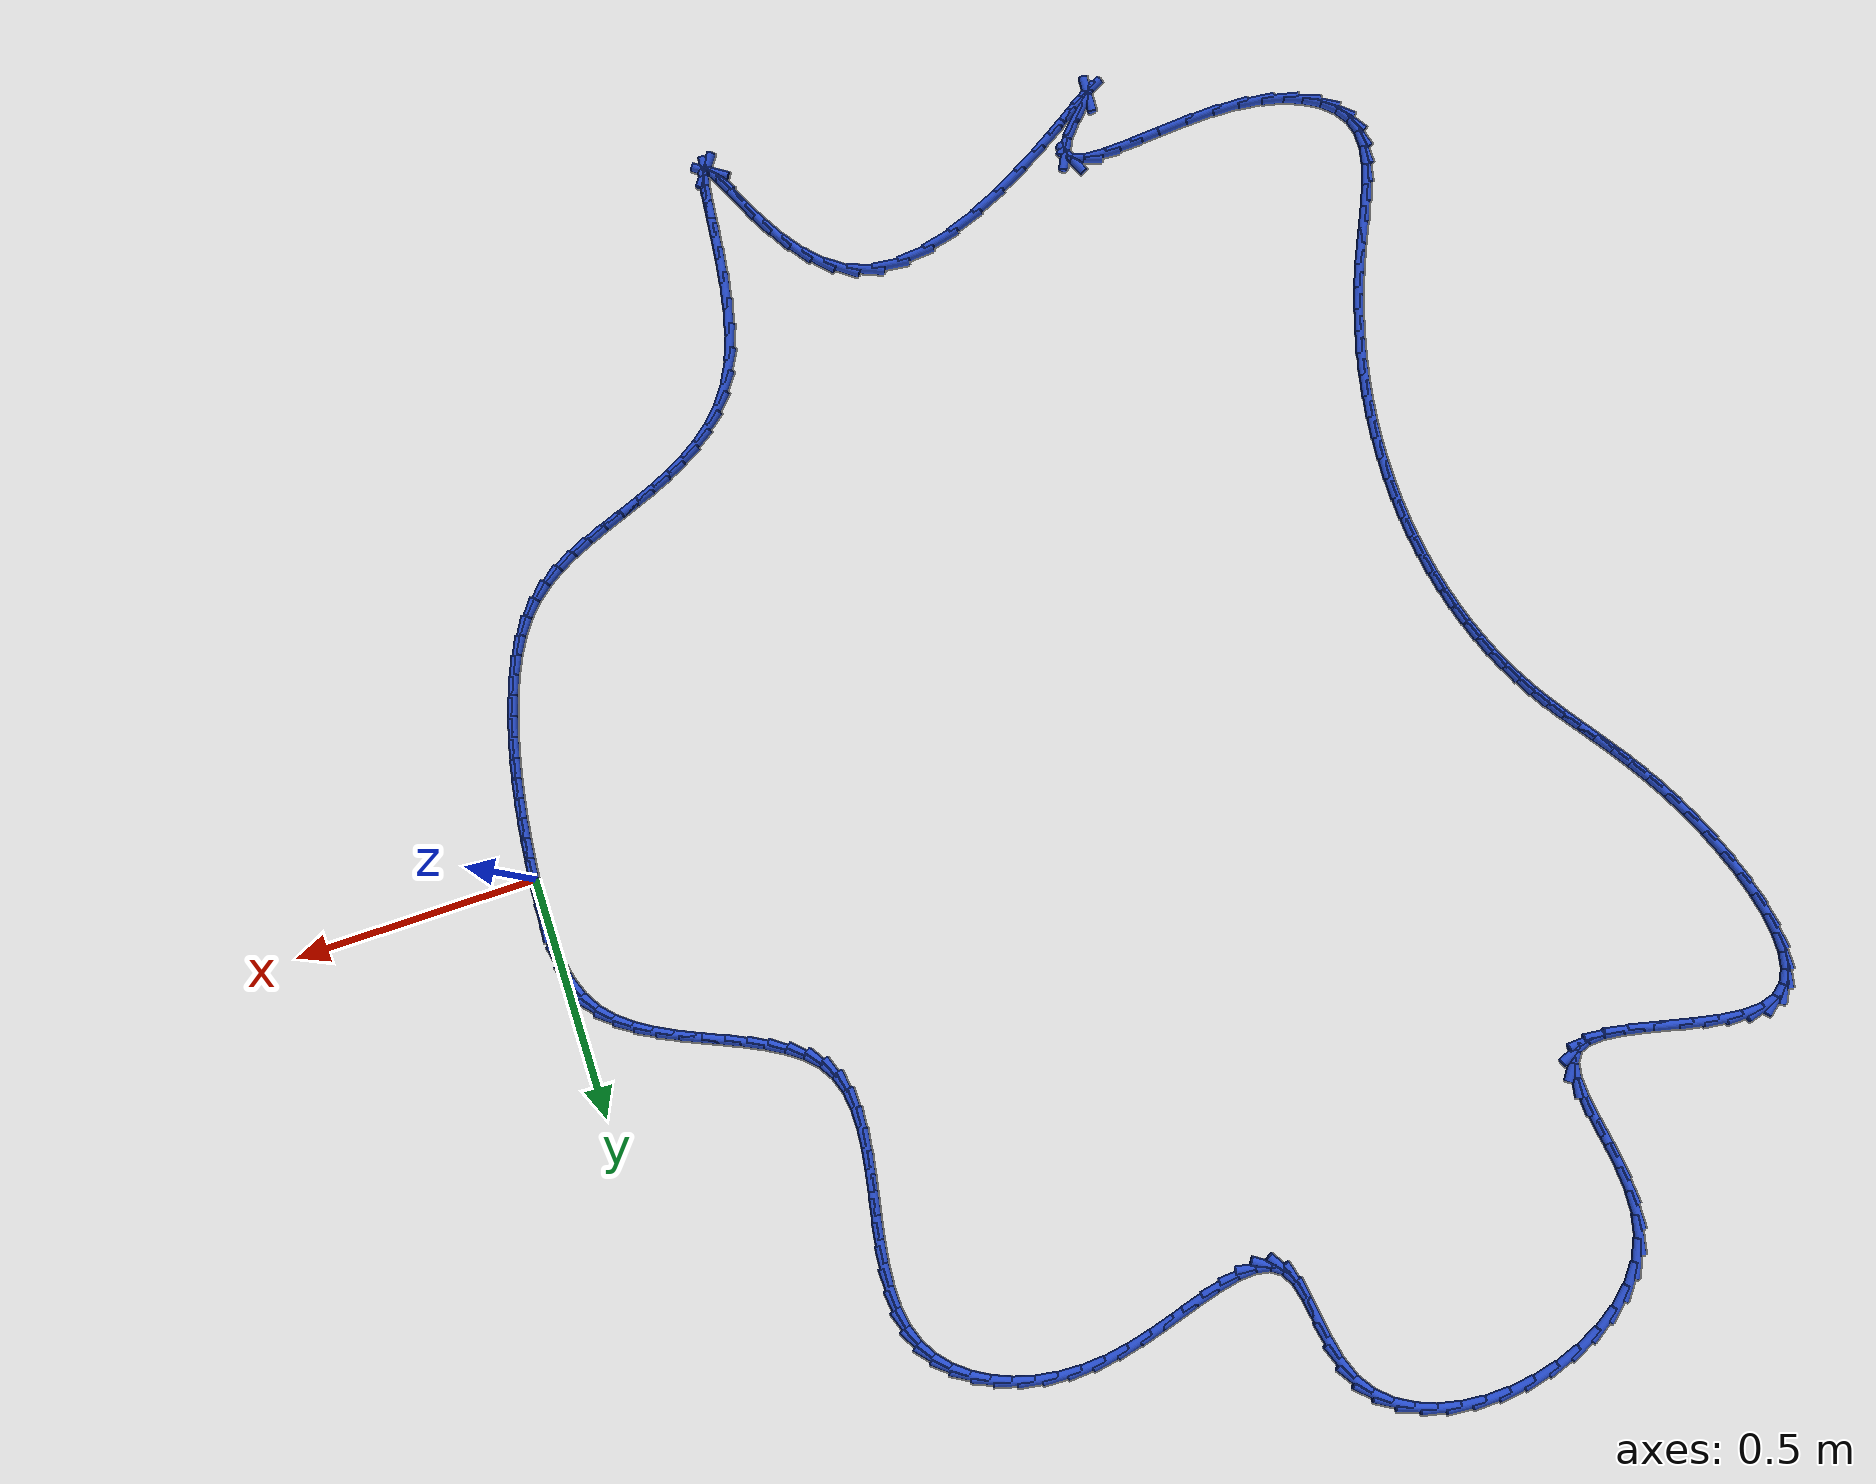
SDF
<sdf version="1.6">
 <world name="default">
  <light name="sun" type="directional">
   <pose>0 0 10 0 -0 0</pose>
   <diffuse>0.8 0.8 0.8 1</diffuse>
   <specular>0.2 0.2 0.2 1</specular>
   <attenuation>
    <range>1000</range>
    <constant>0.9</constant>
    <linear>0.01</linear>
    <quadratic>0.001</quadratic>
   </attenuation>
   <direction>-0.5 0.1 -0.9</direction>
  </light>
  <model name="ground_plane">
   <static>1</static>
   <link name="link">
    <collision name="collision">
     <geometry><plane><normal>0 0 1</normal><size>100 100</size></plane></geometry>
     <surface><friction><ode><mu>100</mu><mu2>50</mu2></ode></friction></surface>
    </collision>
    <visual name="visual">
     <cast_shadows>0</cast_shadows>
     <geometry><plane><normal>0 0 1</normal><size>100 100</size></plane></geometry>
     <material>
      <script><uri>file://media/materials/scripts/gazebo.material</uri><name>Gazebo/WhiteGlow</name></script>
     </material>
    </visual>
   </link>
  </model>
  <gravity>0 0 -9.8</gravity>
  <magnetic_field>6e-06 2.3e-05 -4.2e-05</magnetic_field>
  <atmosphere type="adiabatic"/>
  <physics name="default_physics" default="0" type="ode">
   <max_step_size>0.001</max_step_size>
   <real_time_factor>1</real_time_factor>
   <real_time_update_rate>1000</real_time_update_rate>
  </physics>
  <scene><ambient>0.4 0.4 0.4 1</ambient><background>0.7 0.7 0.7 1</background><shadows>1</shadows></scene>
  <spherical_coordinates>
   <surface_model>EARTH_WGS84</surface_model>
   <latitude_deg>0</latitude_deg>
   <longitude_deg>0</longitude_deg>
   <elevation>0</elevation>
   <heading_deg>0</heading_deg>
  </spherical_coordinates>
  <model name="line">
   <link name="link_0">
    <pose>-1.734723475976807e-18 -6.938893903907228e-17 0.01 0 1.57 1.5075813447620587</pose>
    <collision name="collision">
     <geometry><cylinder><radius>0.01</radius><length>0.08</length></cylinder></geometry>
    </collision>
    <visual name="visual">
     <material>
      <script><name>Gazebo/Blue</name><uri>file://media/materials/scripts/gazebo.material</uri></script>
     </material>
     <geometry><cylinder><radius>0.01</radius><length>0.08</length></cylinder></geometry>
    </visual>
   </link>
   <link name="link_1">
    <pose>0.002784637520736706 0.04399158524193885 0.01 0 1.57 1.5406812396212106</pose>
    <collision name="collision">
     <geometry><cylinder><radius>0.01</radius><length>0.08</length></cylinder></geometry>
    </collision>
    <visual name="visual">
     <material>
      <script><name>Gazebo/Blue</name><uri>file://media/materials/scripts/gazebo.material</uri></script>
     </material>
     <geometry><cylinder><radius>0.01</radius><length>0.08</length></cylinder></geometry>
    </visual>
   </link>
   <link name="link_2">
    <pose>0.004123461948492164 0.08843507832212538 0.01 0 1.57 -1.5465252184194505</pose>
    <collision name="collision">
     <geometry><cylinder><radius>0.01</radius><length>0.08</length></cylinder></geometry>
    </collision>
    <visual name="visual">
     <material>
      <script><name>Gazebo/Blue</name><uri>file://media/materials/scripts/gazebo.material</uri></script>
     </material>
     <geometry><cylinder><radius>0.01</radius><length>0.08</length></cylinder></geometry>
    </visual>
   </link>
   <link name="link_3">
    <pose>0.003054482190493274 0.13246973162138626 0.01 0 1.57 -1.46737225537892</pose>
    <collision name="collision">
     <geometry><cylinder><radius>0.01</radius><length>0.08</length></cylinder></geometry>
    </collision>
    <visual name="visual">
     <material>
      <script><name>Gazebo/Blue</name><uri>file://media/materials/scripts/gazebo.material</uri></script>
     </material>
     <geometry><cylinder><radius>0.01</radius><length>0.08</length></cylinder></geometry>
    </visual>
   </link>
   <link name="link_4">
    <pose>-0.0013842928460330636 0.17523479752054835 0.01 0 1.57 -1.3582183337706233</pose>
    <collision name="collision">
     <geometry><cylinder><radius>0.01</radius><length>0.08</length></cylinder></geometry>
    </collision>
    <visual name="visual">
     <material>
      <script><name>Gazebo/Blue</name><uri>file://media/materials/scripts/gazebo.material</uri></script>
     </material>
     <geometry><cylinder><radius>0.01</radius><length>0.08</length></cylinder></geometry>
    </visual>
   </link>
   <link name="link_5">
    <pose>-0.010154854253859954 0.21586952840043838 0.01 0 1.57 -1.21323795592164</pose>
    <collision name="collision">
     <geometry><cylinder><radius>0.01</radius><length>0.08</length></cylinder></geometry>
    </collision>
    <visual name="visual">
     <material>
      <script><name>Gazebo/Blue</name><uri>file://media/materials/scripts/gazebo.material</uri></script>
     </material>
     <geometry><cylinder><radius>0.01</radius><length>0.08</length></cylinder></geometry>
    </visual>
   </link>
   <link name="link_6">
    <pose>-0.02421919312576048 0.25351317664188305 0.01 0 1.57 -1.0294588875116106</pose>
    <collision name="collision">
     <geometry><cylinder><radius>0.01</radius><length>0.08</length></cylinder></geometry>
    </collision>
    <visual name="visual">
     <material>
      <script><name>Gazebo/Blue</name><uri>file://media/materials/scripts/gazebo.material</uri></script>
     </material>
     <geometry><cylinder><radius>0.01</radius><length>0.08</length></cylinder></geometry>
    </visual>
   </link>
   <link name="link_7">
    <pose>-0.044537344429835014 0.28730641109138877 0.01 0 1.57 -0.8309019516130127</pose>
    <collision name="collision">
     <geometry><cylinder><radius>0.01</radius><length>0.08</length></cylinder></geometry>
    </collision>
    <visual name="visual">
     <material>
      <script><name>Gazebo/Blue</name><uri>file://media/materials/scripts/gazebo.material</uri></script>
     </material>
     <geometry><cylinder><radius>0.01</radius><length>0.08</length></cylinder></geometry>
    </visual>
   </link>
   <link name="link_8">
    <pose>-0.07147826844885385 0.3168179085938486 0.01 0 1.57 -0.6712388561655755</pose>
    <collision name="collision">
     <geometry><cylinder><radius>0.01</radius><length>0.08</length></cylinder></geometry>
    </collision>
    <visual name="visual">
     <material>
      <script><name>Gazebo/Blue</name><uri>file://media/materials/scripts/gazebo.material</uri></script>
     </material>
     <geometry><cylinder><radius>0.01</radius><length>0.08</length></cylinder></geometry>
    </visual>
   </link>
   <link name="link_9">
    <pose>-0.1039927515524356 0.3426432716822239 0.01 0 1.57 -0.5559903240304429</pose>
    <collision name="collision">
     <geometry><cylinder><radius>0.01</radius><length>0.08</length></cylinder></geometry>
    </collision>
    <visual name="visual">
     <material>
      <script><name>Gazebo/Blue</name><uri>file://media/materials/scripts/gazebo.material</uri></script>
     </material>
     <geometry><cylinder><radius>0.01</radius><length>0.08</length></cylinder></geometry>
    </visual>
   </link>
   <link name="link_10">
    <pose>-0.14082327517312274 0.365528940307124 0.01 0 1.57 -0.4785342879646732</pose>
    <collision name="collision">
     <geometry><cylinder><radius>0.01</radius><length>0.08</length></cylinder></geometry>
    </collision>
    <visual name="visual">
     <material>
      <script><name>Gazebo/Blue</name><uri>file://media/materials/scripts/gazebo.material</uri></script>
     </material>
     <geometry><cylinder><radius>0.01</radius><length>0.08</length></cylinder></geometry>
    </visual>
   </link>
   <link name="link_11">
    <pose>-0.18071232074345772 0.3862213544191577 0.01 0 1.57 -0.43248763090904774</pose>
    <collision name="collision">
     <geometry><cylinder><radius>0.01</radius><length>0.08</length></cylinder></geometry>
    </collision>
    <visual name="visual">
     <material>
      <script><name>Gazebo/Blue</name><uri>file://media/materials/scripts/gazebo.material</uri></script>
     </material>
     <geometry><cylinder><radius>0.01</radius><length>0.08</length></cylinder></geometry>
    </visual>
   </link>
   <link name="link_12">
    <pose>-0.22240236969598312 0.40546695396893434 0.01 0 1.57 -0.4137621364217773</pose>
    <collision name="collision">
     <geometry><cylinder><radius>0.01</radius><length>0.08</length></cylinder></geometry>
    </collision>
    <visual name="visual">
     <material>
      <script><name>Gazebo/Blue</name><uri>file://media/materials/scripts/gazebo.material</uri></script>
     </material>
     <geometry><cylinder><radius>0.01</radius><length>0.08</length></cylinder></geometry>
    </visual>
   </link>
   <link name="link_13">
    <pose>-0.2646359034632414 0.424012178907063 0.01 0 1.57 -0.4209999911419791</pose>
    <collision name="collision">
     <geometry><cylinder><radius>0.01</radius><length>0.08</length></cylinder></geometry>
    </collision>
    <visual name="visual">
     <material>
      <script><name>Gazebo/Blue</name><uri>file://media/materials/scripts/gazebo.material</uri></script>
     </material>
     <geometry><cylinder><radius>0.01</radius><length>0.08</length></cylinder></geometry>
    </visual>
   </link>
   <link name="link_14">
    <pose>-0.306155403477775 0.4426034691841526 0.01 0 1.57 -0.4557237394077343</pose>
    <collision name="collision">
     <geometry><cylinder><radius>0.01</radius><length>0.08</length></cylinder></geometry>
    </collision>
    <visual name="visual">
     <material>
      <script><name>Gazebo/Blue</name><uri>file://media/materials/scripts/gazebo.material</uri></script>
     </material>
     <geometry><cylinder><radius>0.01</radius><length>0.08</length></cylinder></geometry>
    </visual>
   </link>
   <link name="link_15">
    <pose>-0.34570335117212647 0.46198726475081253 0.01 0 1.57 -0.5226489040140722</pose>
    <collision name="collision">
     <geometry><cylinder><radius>0.01</radius><length>0.08</length></cylinder></geometry>
    </collision>
    <visual name="visual">
     <material>
      <script><name>Gazebo/Blue</name><uri>file://media/materials/scripts/gazebo.material</uri></script>
     </material>
     <geometry><cylinder><radius>0.01</radius><length>0.08</length></cylinder></geometry>
    </visual>
   </link>
   <link name="link_16">
    <pose>-0.38202222797883817 0.4829100055576516 0.01 0 1.57 -0.6299740824482429</pose>
    <collision name="collision">
     <geometry><cylinder><radius>0.01</radius><length>0.08</length></cylinder></geometry>
    </collision>
    <visual name="visual">
     <material>
      <script><name>Gazebo/Blue</name><uri>file://media/materials/scripts/gazebo.material</uri></script>
     </material>
     <geometry><cylinder><radius>0.01</radius><length>0.08</length></cylinder></geometry>
    </visual>
   </link>
   <link name="link_17">
    <pose>-0.4138545153304529 0.5061181315552792 0.01 0 1.57 -0.788298541894239</pose>
    <collision name="collision">
     <geometry><cylinder><radius>0.01</radius><length>0.08</length></cylinder></geometry>
    </collision>
    <visual name="visual">
     <material>
      <script><name>Gazebo/Blue</name><uri>file://media/materials/scripts/gazebo.material</uri></script>
     </material>
     <geometry><cylinder><radius>0.01</radius><length>0.08</length></cylinder></geometry>
    </visual>
   </link>
   <link name="link_18">
    <pose>-0.43994269465951275 0.5323580826943042 0.01 0 1.57 -1.0038657184812607</pose>
    <collision name="collision">
     <geometry><cylinder><radius>0.01</radius><length>0.08</length></cylinder></geometry>
    </collision>
    <visual name="visual">
     <material>
      <script><name>Gazebo/Blue</name><uri>file://media/materials/scripts/gazebo.material</uri></script>
     </material>
     <geometry><cylinder><radius>0.01</radius><length>0.08</length></cylinder></geometry>
    </visual>
   </link>
   <link name="link_19">
    <pose>-0.45904732088133976 0.5623662939539198 0.01 0 1.57 -1.2364906010532806</pose>
    <collision name="collision">
     <geometry><cylinder><radius>0.01</radius><length>0.08</length></cylinder></geometry>
    </collision>
    <visual name="visual">
     <material>
      <script><name>Gazebo/Blue</name><uri>file://media/materials/scripts/gazebo.material</uri></script>
     </material>
     <geometry><cylinder><radius>0.01</radius><length>0.08</length></cylinder></geometry>
    </visual>
   </link>
   <link name="link_20">
    <pose>-0.47085673879814094 0.5963656019431754 0.01 0 1.57 -1.423534688620045</pose>
    <collision name="collision">
     <geometry><cylinder><radius>0.01</radius><length>0.08</length></cylinder></geometry>
    </collision>
    <visual name="visual">
     <material>
      <script><name>Gazebo/Blue</name><uri>file://media/materials/scripts/gazebo.material</uri></script>
     </material>
     <geometry><cylinder><radius>0.01</radius><length>0.08</length></cylinder></geometry>
    </visual>
   </link>
   <link name="link_21">
    <pose>-0.4764138859928321 0.633828978830674 0.01 0 1.57 -1.5595155047964435</pose>
    <collision name="collision">
     <geometry><cylinder><radius>0.01</radius><length>0.08</length></cylinder></geometry>
    </collision>
    <visual name="visual">
     <material>
      <script><name>Gazebo/Blue</name><uri>file://media/materials/scripts/gazebo.material</uri></script>
     </material>
     <geometry><cylinder><radius>0.01</radius><length>0.08</length></cylinder></geometry>
    </visual>
   </link>
   <link name="link_22">
    <pose>-0.476868985252644 0.6741700067152891 0.01 0 1.57 1.488958863091157</pose>
    <collision name="collision">
     <geometry><cylinder><radius>0.01</radius><length>0.08</length></cylinder></geometry>
    </collision>
    <visual name="visual">
     <material>
      <script><name>Gazebo/Blue</name><uri>file://media/materials/scripts/gazebo.material</uri></script>
     </material>
     <geometry><cylinder><radius>0.01</radius><length>0.08</length></cylinder></geometry>
    </visual>
   </link>
   <link name="link_23">
    <pose>-0.4733722593648075 0.7168022676958943 0.01 0 1.57 1.4296849099934554</pose>
    <collision name="collision">
     <geometry><cylinder><radius>0.01</radius><length>0.08</length></cylinder></geometry>
    </collision>
    <visual name="visual">
     <material>
      <script><name>Gazebo/Blue</name><uri>file://media/materials/scripts/gazebo.material</uri></script>
     </material>
     <geometry><cylinder><radius>0.01</radius><length>0.08</length></cylinder></geometry>
    </visual>
   </link>
   <link name="link_24">
    <pose>-0.4670739311165533 0.761139343871363 0.01 0 1.57 1.3976573922703521</pose>
    <collision name="collision">
     <geometry><cylinder><radius>0.01</radius><length>0.08</length></cylinder></geometry>
    </collision>
    <visual name="visual">
     <material>
      <script><name>Gazebo/Blue</name><uri>file://media/materials/scripts/gazebo.material</uri></script>
     </material>
     <geometry><cylinder><radius>0.01</radius><length>0.08</length></cylinder></geometry>
    </visual>
   </link>
   <link name="link_25">
    <pose>-0.45912422329511204 0.8065948173405679 0.01 0 1.57 1.389059368427677</pose>
    <collision name="collision">
     <geometry><cylinder><radius>0.01</radius><length>0.08</length></cylinder></geometry>
    </collision>
    <visual name="visual">
     <material>
      <script><name>Gazebo/Blue</name><uri>file://media/materials/scripts/gazebo.material</uri></script>
     </material>
     <geometry><cylinder><radius>0.01</radius><length>0.08</length></cylinder></geometry>
    </visual>
   </link>
   <link name="link_26">
    <pose>-0.45067335868771474 0.8525822702023832 0.01 0 1.57 1.402550349332435</pose>
    <collision name="collision">
     <geometry><cylinder><radius>0.01</radius><length>0.08</length></cylinder></geometry>
    </collision>
    <visual name="visual">
     <material>
      <script><name>Gazebo/Blue</name><uri>file://media/materials/scripts/gazebo.material</uri></script>
     </material>
     <geometry><cylinder><radius>0.01</radius><length>0.08</length></cylinder></geometry>
    </visual>
   </link>
   <link name="link_27">
    <pose>-0.44287156008159206 0.8985152845556821 0.01 0 1.57 1.439035477866174</pose>
    <collision name="collision">
     <geometry><cylinder><radius>0.01</radius><length>0.08</length></cylinder></geometry>
    </collision>
    <visual name="visual">
     <material>
      <script><name>Gazebo/Blue</name><uri>file://media/materials/scripts/gazebo.material</uri></script>
     </material>
     <geometry><cylinder><radius>0.01</radius><length>0.08</length></cylinder></geometry>
    </visual>
   </link>
   <link name="link_28">
    <pose>-0.43686905026397466 0.9438074424993376 0.01 0 1.57 1.5016227147052752</pose>
    <collision name="collision">
     <geometry><cylinder><radius>0.01</radius><length>0.08</length></cylinder></geometry>
    </collision>
    <visual name="visual">
     <material>
      <script><name>Gazebo/Blue</name><uri>file://media/materials/scripts/gazebo.material</uri></script>
     </material>
     <geometry><cylinder><radius>0.01</radius><length>0.08</length></cylinder></geometry>
    </visual>
   </link>
   <link name="link_29">
    <pose>-0.4338160520220934 0.9878723261322235 0.01 0 1.57 -1.5460272725389976</pose>
    <collision name="collision">
     <geometry><cylinder><radius>0.01</radius><length>0.08</length></cylinder></geometry>
    </collision>
    <visual name="visual">
     <material>
      <script><name>Gazebo/Blue</name><uri>file://media/materials/scripts/gazebo.material</uri></script>
     </material>
     <geometry><cylinder><radius>0.01</radius><length>0.08</length></cylinder></geometry>
    </visual>
   </link>
   <link name="link_30">
    <pose>-0.43486278814317914 1.0301235175532133 0.01 0 1.57 -1.4140863033260147</pose>
    <collision name="collision">
     <geometry><cylinder><radius>0.01</radius><length>0.08</length></cylinder></geometry>
    </collision>
    <visual name="visual">
     <material>
      <script><name>Gazebo/Blue</name><uri>file://media/materials/scripts/gazebo.material</uri></script>
     </material>
     <geometry><cylinder><radius>0.01</radius><length>0.08</length></cylinder></geometry>
    </visual>
   </link>
   <link name="link_31">
    <pose>-0.4411594814144624 1.0699745988611804 0.01 0 1.57 -1.2391766451692432</pose>
    <collision name="collision">
     <geometry><cylinder><radius>0.01</radius><length>0.08</length></cylinder></geometry>
    </collision>
    <visual name="visual">
     <material>
      <script><name>Gazebo/Blue</name><uri>file://media/materials/scripts/gazebo.material</uri></script>
     </material>
     <geometry><cylinder><radius>0.01</radius><length>0.08</length></cylinder></geometry>
    </visual>
   </link>
   <link name="link_32">
    <pose>-0.4538534423257002 1.1068396850951172 0.01 0 1.57 -1.0378144487902856</pose>
    <collision name="collision">
     <geometry><cylinder><radius>0.01</radius><length>0.08</length></cylinder></geometry>
    </collision>
    <visual name="visual">
     <material>
      <script><name>Gazebo/Blue</name><uri>file://media/materials/scripts/gazebo.material</uri></script>
     </material>
     <geometry><cylinder><radius>0.01</radius><length>0.08</length></cylinder></geometry>
    </visual>
   </link>
   <link name="link_33">
    <pose>-0.4735523460815084 1.140231642639307 0.01 0 1.57 -0.8480839209278062</pose>
    <collision name="collision">
     <geometry><cylinder><radius>0.01</radius><length>0.08</length></cylinder></geometry>
    </collision>
    <visual name="visual">
     <material>
      <script><name>Gazebo/Blue</name><uri>file://media/materials/scripts/gazebo.material</uri></script>
     </material>
     <geometry><cylinder><radius>0.01</radius><length>0.08</length></cylinder></geometry>
    </visual>
   </link>
   <link name="link_34">
    <pose>-0.49969599131086123 1.1698770551536672 0.01 0 1.57 -0.6776585721044397</pose>
    <collision name="collision">
     <geometry><cylinder><radius>0.01</radius><length>0.08</length></cylinder></geometry>
    </collision>
    <visual name="visual">
     <material>
      <script><name>Gazebo/Blue</name><uri>file://media/materials/scripts/gazebo.material</uri></script>
     </material>
     <geometry><cylinder><radius>0.01</radius><length>0.08</length></cylinder></geometry>
    </visual>
   </link>
   <link name="link_35">
    <pose>-0.5315716059665438 1.195530426191311 0.01 0 1.57 -0.5259253081681029</pose>
    <collision name="collision">
     <geometry><cylinder><radius>0.01</radius><length>0.08</length></cylinder></geometry>
    </collision>
    <visual name="visual">
     <material>
      <script><name>Gazebo/Blue</name><uri>file://media/materials/scripts/gazebo.material</uri></script>
     </material>
     <geometry><cylinder><radius>0.01</radius><length>0.08</length></cylinder></geometry>
    </visual>
   </link>
   <link name="link_36">
    <pose>-0.5684664180013407 1.2169462593053495 0.01 0 1.57 -0.3899341303063244</pose>
    <collision name="collision">
     <geometry><cylinder><radius>0.01</radius><length>0.08</length></cylinder></geometry>
    </collision>
    <visual name="visual">
     <material>
      <script><name>Gazebo/Blue</name><uri>file://media/materials/scripts/gazebo.material</uri></script>
     </material>
     <geometry><cylinder><radius>0.01</radius><length>0.08</length></cylinder></geometry>
    </visual>
   </link>
   <link name="link_37">
    <pose>-0.6096676553680375 1.2338790580488967 0.01 0 1.57 -0.26599187526635876</pose>
    <collision name="collision">
     <geometry><cylinder><radius>0.01</radius><length>0.08</length></cylinder></geometry>
    </collision>
    <visual name="visual">
     <material>
      <script><name>Gazebo/Blue</name><uri>file://media/materials/scripts/gazebo.material</uri></script>
     </material>
     <geometry><cylinder><radius>0.01</radius><length>0.08</length></cylinder></geometry>
    </visual>
   </link>
   <link name="link_38">
    <pose>-0.6544625460194189 1.2460833259750648 0.01 0 1.57 -0.15050755038997266</pose>
    <collision name="collision">
     <geometry><cylinder><radius>0.01</radius><length>0.08</length></cylinder></geometry>
    </collision>
    <visual name="visual">
     <material>
      <script><name>Gazebo/Blue</name><uri>file://media/materials/scripts/gazebo.material</uri></script>
     </material>
     <geometry><cylinder><radius>0.01</radius><length>0.08</length></cylinder></geometry>
    </visual>
   </link>
   <link name="link_39">
    <pose>-0.70213831790827 1.2533135666369666 0.01 0 1.57 -0.04031843557476348</pose>
    <collision name="collision">
     <geometry><cylinder><radius>0.01</radius><length>0.08</length></cylinder></geometry>
    </collision>
    <visual name="visual">
     <material>
      <script><name>Gazebo/Blue</name><uri>file://media/materials/scripts/gazebo.material</uri></script>
     </material>
     <geometry><cylinder><radius>0.01</radius><length>0.08</length></cylinder></geometry>
    </visual>
   </link>
   <link name="link_40">
    <pose>-0.7519821989873758 1.2553242835877143 0.01 0 1.57 0.06723389349264446</pose>
    <collision name="collision">
     <geometry><cylinder><radius>0.01</radius><length>0.08</length></cylinder></geometry>
    </collision>
    <visual name="visual">
     <material>
      <script><name>Gazebo/Blue</name><uri>file://media/materials/scripts/gazebo.material</uri></script>
     </material>
     <geometry><cylinder><radius>0.01</radius><length>0.08</length></cylinder></geometry>
    </visual>
   </link>
   <link name="link_41">
    <pose>-0.8032814110767225 1.2518700313935303 0.01 0 1.57 0.16664566558850424</pose>
    <collision name="collision">
     <geometry><cylinder><radius>0.01</radius><length>0.08</length></cylinder></geometry>
    </collision>
    <visual name="visual">
     <material>
      <script><name>Gazebo/Blue</name><uri>file://media/materials/scripts/gazebo.material</uri></script>
     </material>
     <geometry><cylinder><radius>0.01</radius><length>0.08</length></cylinder></geometry>
    </visual>
   </link>
   <link name="link_42">
    <pose>-0.8552727519905432 1.2431247955065161 0.01 0 1.57 0.23567779062867336</pose>
    <collision name="collision">
     <geometry><cylinder><radius>0.01</radius><length>0.08</length></cylinder></geometry>
    </collision>
    <visual name="visual">
     <material>
      <script><name>Gazebo/Blue</name><uri>file://media/materials/scripts/gazebo.material</uri></script>
     </material>
     <geometry><cylinder><radius>0.01</radius><length>0.08</length></cylinder></geometry>
    </visual>
   </link>
   <link name="link_43">
    <pose>-0.9070204412434096 1.2306980813861648 0.01 0 1.57 0.2737984781586707</pose>
    <collision name="collision">
     <geometry><cylinder><radius>0.01</radius><length>0.08</length></cylinder></geometry>
    </collision>
    <visual name="visual">
     <material>
      <script><name>Gazebo/Blue</name><uri>file://media/materials/scripts/gazebo.material</uri></script>
     </material>
     <geometry><cylinder><radius>0.01</radius><length>0.08</length></cylinder></geometry>
    </visual>
   </link>
   <link name="link_44">
    <pose>-0.9575518079279015 1.2165062519529262 0.01 0 1.57 0.2826636786365664</pose>
    <collision name="collision">
     <geometry><cylinder><radius>0.01</radius><length>0.08</length></cylinder></geometry>
    </collision>
    <visual name="visual">
     <material>
      <script><name>Gazebo/Blue</name><uri>file://media/materials/scripts/gazebo.material</uri></script>
     </material>
     <geometry><cylinder><radius>0.01</radius><length>0.08</length></cylinder></geometry>
    </visual>
   </link>
   <link name="link_45">
    <pose>-1.005894181136599 1.20246567012725 0.01 0 1.57 0.25904745650340677</pose>
    <collision name="collision">
     <geometry><cylinder><radius>0.01</radius><length>0.08</length></cylinder></geometry>
    </collision>
    <visual name="visual">
     <material>
      <script><name>Gazebo/Blue</name><uri>file://media/materials/scripts/gazebo.material</uri></script>
     </material>
     <geometry><cylinder><radius>0.01</radius><length>0.08</length></cylinder></geometry>
    </visual>
   </link>
   <link name="link_46">
    <pose>-1.0510748899620814 1.1904926988295865 0.01 0 1.57 0.19223014374212394</pose>
    <collision name="collision">
     <geometry><cylinder><radius>0.01</radius><length>0.08</length></cylinder></geometry>
    </collision>
    <visual name="visual">
     <material>
      <script><name>Gazebo/Blue</name><uri>file://media/materials/scripts/gazebo.material</uri></script>
     </material>
     <geometry><cylinder><radius>0.01</radius><length>0.08</length></cylinder></geometry>
    </visual>
   </link>
   <link name="link_47">
    <pose>-1.0921212634969284 1.182503700980385 0.01 0 1.57 0.05805095928286429</pose>
    <collision name="collision">
     <geometry><cylinder><radius>0.01</radius><length>0.08</length></cylinder></geometry>
    </collision>
    <visual name="visual">
     <material>
      <script><name>Gazebo/Blue</name><uri>file://media/materials/scripts/gazebo.material</uri></script>
     </material>
     <geometry><cylinder><radius>0.01</radius><length>0.08</length></cylinder></geometry>
    </visual>
   </link>
   <link name="link_48">
    <pose>-1.1280606308337198 1.1804150395000956 0.01 0 1.57 -0.18952931685719568</pose>
    <collision name="collision">
     <geometry><cylinder><radius>0.01</radius><length>0.08</length></cylinder></geometry>
    </collision>
    <visual name="visual">
     <material>
      <script><name>Gazebo/Blue</name><uri>file://media/materials/scripts/gazebo.material</uri></script>
     </material>
     <geometry><cylinder><radius>0.01</radius><length>0.08</length></cylinder></geometry>
    </visual>
   </link>
   <link name="link_49">
    <pose>-1.1579203210650353 1.1861430773091683 0.01 0 1.57 -0.595739341852695</pose>
    <collision name="collision">
     <geometry><cylinder><radius>0.01</radius><length>0.08</length></cylinder></geometry>
    </collision>
    <visual name="visual">
     <material>
      <script><name>Gazebo/Blue</name><uri>file://media/materials/scripts/gazebo.material</uri></script>
     </material>
     <geometry><cylinder><radius>0.01</radius><length>0.08</length></cylinder></geometry>
    </visual>
   </link>
   <link name="link_50">
    <pose>-1.180727663283455 1.2016041773280535 0.01 0 1.57 -1.056575846274085</pose>
    <collision name="collision">
     <geometry><cylinder><radius>0.01</radius><length>0.08</length></cylinder></geometry>
    </collision>
    <visual name="visual">
     <material>
      <script><name>Gazebo/Blue</name><uri>file://media/materials/scripts/gazebo.material</uri></script>
     </material>
     <geometry><cylinder><radius>0.01</radius><length>0.08</length></cylinder></geometry>
    </visual>
   </link>
   <link name="link_51">
    <pose>-1.195817657465123 1.2283162517087955 0.01 0 1.57 -1.3226920176395807</pose>
    <collision name="collision">
     <geometry><cylinder><radius>0.01</radius><length>0.08</length></cylinder></geometry>
    </collision>
    <visual name="visual">
     <material>
      <script><name>Gazebo/Blue</name><uri>file://media/materials/scripts/gazebo.material</uri></script>
     </material>
     <geometry><cylinder><radius>0.01</radius><length>0.08</length></cylinder></geometry>
    </visual>
   </link>
   <link name="link_52">
    <pose>-1.2050054575980225 1.264585276328136 0.01 0 1.57 -1.423941028695141</pose>
    <collision name="collision">
     <geometry><cylinder><radius>0.01</radius><length>0.08</length></cylinder></geometry>
    </collision>
    <visual name="visual">
     <material>
      <script><name>Gazebo/Blue</name><uri>file://media/materials/scripts/gazebo.material</uri></script>
     </material>
     <geometry><cylinder><radius>0.01</radius><length>0.08</length></cylinder></geometry>
    </visual>
   </link>
   <link name="link_53">
    <pose>-1.211304009851146 1.307166020106271 0.01 0 1.57 -1.4308234794827706</pose>
    <collision name="collision">
     <geometry><cylinder><radius>0.01</radius><length>0.08</length></cylinder></geometry>
    </collision>
    <visual name="visual">
     <material>
      <script><name>Gazebo/Blue</name><uri>file://media/materials/scripts/gazebo.material</uri></script>
     </material>
     <geometry><cylinder><radius>0.01</radius><length>0.08</length></cylinder></geometry>
    </visual>
   </link>
   <link name="link_54">
    <pose>-1.2177340236779317 1.3528031980817412 0.01 0 1.57 -1.3629582814847445</pose>
    <collision name="collision">
     <geometry><cylinder><radius>0.01</radius><length>0.08</length></cylinder></geometry>
    </collision>
    <visual name="visual">
     <material>
      <script><name>Gazebo/Blue</name><uri>file://media/materials/scripts/gazebo.material</uri></script>
     </material>
     <geometry><cylinder><radius>0.01</radius><length>0.08</length></cylinder></geometry>
    </visual>
   </link>
   <link name="link_55">
    <pose>-1.2273162085318172 1.398241525293087 0.01 0 1.57 -1.211796109861053</pose>
    <collision name="collision">
     <geometry><cylinder><radius>0.01</radius><length>0.08</length></cylinder></geometry>
    </collision>
    <visual name="visual">
     <material>
      <script><name>Gazebo/Blue</name><uri>file://media/materials/scripts/gazebo.material</uri></script>
     </material>
     <geometry><cylinder><radius>0.01</radius><length>0.08</length></cylinder></geometry>
    </visual>
   </link>
   <link name="link_56">
    <pose>-1.2430712738662402 1.4402257167788477 0.01 0 1.57 -0.9751484173841496</pose>
    <collision name="collision">
     <geometry><cylinder><radius>0.01</radius><length>0.08</length></cylinder></geometry>
    </collision>
    <visual name="visual">
     <material>
      <script><name>Gazebo/Blue</name><uri>file://media/materials/scripts/gazebo.material</uri></script>
     </material>
     <geometry><cylinder><radius>0.01</radius><length>0.08</length></cylinder></geometry>
    </visual>
   </link>
   <link name="link_57">
    <pose>-1.2673439345193092 1.4760384255572954 0.01 0 1.57 -0.7354734577616764</pose>
    <collision name="collision">
     <geometry><cylinder><radius>0.01</radius><length>0.08</length></cylinder></geometry>
    </collision>
    <visual name="visual">
     <material>
      <script><name>Gazebo/Blue</name><uri>file://media/materials/scripts/gazebo.material</uri></script>
     </material>
     <geometry><cylinder><radius>0.01</radius><length>0.08</length></cylinder></geometry>
    </visual>
   </link>
   <link name="link_58">
    <pose>-1.2996169337274308 1.505239783174713 0.01 0 1.57 -0.5281404327485768</pose>
    <collision name="collision">
     <geometry><cylinder><radius>0.01</radius><length>0.08</length></cylinder></geometry>
    </collision>
    <visual name="visual">
     <material>
      <script><name>Gazebo/Blue</name><uri>file://media/materials/scripts/gazebo.material</uri></script>
     </material>
     <geometry><cylinder><radius>0.01</radius><length>0.08</length></cylinder></geometry>
    </visual>
   </link>
   <link name="link_59">
    <pose>-1.338615742700818 1.5279925374921302 0.01 0 1.57 -0.3547829683620413</pose>
    <collision name="collision">
     <geometry><cylinder><radius>0.01</radius><length>0.08</length></cylinder></geometry>
    </collision>
    <visual name="visual">
     <material>
      <script><name>Gazebo/Blue</name><uri>file://media/materials/scripts/gazebo.material</uri></script>
     </material>
     <geometry><cylinder><radius>0.01</radius><length>0.08</length></cylinder></geometry>
    </visual>
   </link>
   <link name="link_60">
    <pose>-1.3830658277974845 1.5444594402318201 0.01 0 1.57 -0.2095939920211379</pose>
    <collision name="collision">
     <geometry><cylinder><radius>0.01</radius><length>0.08</length></cylinder></geometry>
    </collision>
    <visual name="visual">
     <material>
      <script><name>Gazebo/Blue</name><uri>file://media/materials/scripts/gazebo.material</uri></script>
     </material>
     <geometry><cylinder><radius>0.01</radius><length>0.08</length></cylinder></geometry>
    </visual>
   </link>
   <link name="link_61">
    <pose>-1.4316926553754477 1.5548032431160592 0.01 0 1.57 -0.0848633526750717</pose>
    <collision name="collision">
     <geometry><cylinder><radius>0.01</radius><length>0.08</length></cylinder></geometry>
    </collision>
    <visual name="visual">
     <material>
      <script><name>Gazebo/Blue</name><uri>file://media/materials/scripts/gazebo.material</uri></script>
     </material>
     <geometry><cylinder><radius>0.01</radius><length>0.08</length></cylinder></geometry>
    </visual>
   </link>
   <link name="link_62">
    <pose>-1.4832216917927208 1.5591866978671198 0.01 0 1.57 0.026596983650536036</pose>
    <collision name="collision">
     <geometry><cylinder><radius>0.01</radius><length>0.08</length></cylinder></geometry>
    </collision>
    <visual name="visual">
     <material>
      <script><name>Gazebo/Blue</name><uri>file://media/materials/scripts/gazebo.material</uri></script>
     </material>
     <geometry><cylinder><radius>0.01</radius><length>0.08</length></cylinder></geometry>
    </visual>
   </link>
   <link name="link_63">
    <pose>-1.5363784034073211 1.557772556207277 0.01 0 1.57 0.1309783254316083</pose>
    <collision name="collision">
     <geometry><cylinder><radius>0.01</radius><length>0.08</length></cylinder></geometry>
    </collision>
    <visual name="visual">
     <material>
      <script><name>Gazebo/Blue</name><uri>file://media/materials/scripts/gazebo.material</uri></script>
     </material>
     <geometry><cylinder><radius>0.01</radius><length>0.08</length></cylinder></geometry>
    </visual>
   </link>
   <link name="link_64">
    <pose>-1.589888256577263 1.5507235698588053 0.01 0 1.57 0.2337434895289354</pose>
    <collision name="collision">
     <geometry><cylinder><radius>0.01</radius><length>0.08</length></cylinder></geometry>
    </collision>
    <visual name="visual">
     <material>
      <script><name>Gazebo/Blue</name><uri>file://media/materials/scripts/gazebo.material</uri></script>
     </material>
     <geometry><cylinder><radius>0.01</radius><length>0.08</length></cylinder></geometry>
    </visual>
   </link>
   <link name="link_65">
    <pose>-1.6424767176605615 1.5382024905439788 0.01 0 1.57 0.34008328821273814</pose>
    <collision name="collision">
     <geometry><cylinder><radius>0.01</radius><length>0.08</length></cylinder></geometry>
    </collision>
    <visual name="visual">
     <material>
      <script><name>Gazebo/Blue</name><uri>file://media/materials/scripts/gazebo.material</uri></script>
     </material>
     <geometry><cylinder><radius>0.01</radius><length>0.08</length></cylinder></geometry>
    </visual>
   </link>
   <link name="link_66">
    <pose>-1.6928692530152334 1.5203720699850714 0.01 0 1.57 0.4553611508947169</pose>
    <collision name="collision">
     <geometry><cylinder><radius>0.01</radius><length>0.08</length></cylinder></geometry>
    </collision>
    <visual name="visual">
     <material>
      <script><name>Gazebo/Blue</name><uri>file://media/materials/scripts/gazebo.material</uri></script>
     </material>
     <geometry><cylinder><radius>0.01</radius><length>0.08</length></cylinder></geometry>
    </visual>
   </link>
   <link name="link_67">
    <pose>-1.7397913289992926 1.4973950599043584 0.01 0 1.57 0.5854177110284497</pose>
    <collision name="collision">
     <geometry><cylinder><radius>0.01</radius><length>0.08</length></cylinder></geometry>
    </collision>
    <visual name="visual">
     <material>
      <script><name>Gazebo/Blue</name><uri>file://media/materials/scripts/gazebo.material</uri></script>
     </material>
     <geometry><cylinder><radius>0.01</radius><length>0.08</length></cylinder></geometry>
    </visual>
   </link>
   <link name="link_68">
    <pose>-1.7819684119707557 1.4694342120241128 0.01 0 1.57 0.7364722364024734</pose>
    <collision name="collision">
     <geometry><cylinder><radius>0.01</radius><length>0.08</length></cylinder></geometry>
    </collision>
    <visual name="visual">
     <material>
      <script><name>Gazebo/Blue</name><uri>file://media/materials/scripts/gazebo.material</uri></script>
     </material>
     <geometry><cylinder><radius>0.01</radius><length>0.08</length></cylinder></geometry>
    </visual>
   </link>
   <link name="link_69">
    <pose>-1.8181259682876365 1.4366522780666102 0.01 0 1.57 0.9140395593066732</pose>
    <collision name="collision">
     <geometry><cylinder><radius>0.01</radius><length>0.08</length></cylinder></geometry>
    </collision>
    <visual name="visual">
     <material>
      <script><name>Gazebo/Blue</name><uri>file://media/materials/scripts/gazebo.material</uri></script>
     </material>
     <geometry><cylinder><radius>0.01</radius><length>0.08</length></cylinder></geometry>
    </visual>
   </link>
   <link name="link_70">
    <pose>-1.846989464307952 1.3992120097541239 0.01 0 1.57 1.1200700555077303</pose>
    <collision name="collision">
     <geometry><cylinder><radius>0.01</radius><length>0.08</length></cylinder></geometry>
    </collision>
    <visual name="visual">
     <material>
      <script><name>Gazebo/Blue</name><uri>file://media/materials/scripts/gazebo.material</uri></script>
     </material>
     <geometry><cylinder><radius>0.01</radius><length>0.08</length></cylinder></geometry>
    </visual>
   </link>
   <link name="link_71">
    <pose>-1.8672843663897167 1.3572761588089288 0.01 0 1.57 1.3420315631926252</pose>
    <collision name="collision">
     <geometry><cylinder><radius>0.01</radius><length>0.08</length></cylinder></geometry>
    </collision>
    <visual name="visual">
     <material>
      <script><name>Gazebo/Blue</name><uri>file://media/materials/scripts/gazebo.material</uri></script>
     </material>
     <geometry><cylinder><radius>0.01</radius><length>0.08</length></cylinder></geometry>
    </visual>
   </link>
   <link name="link_72">
    <pose>-1.8780288161068972 1.3111311080971417 0.01 0 1.57 1.5189065009422862</pose>
    <collision name="collision">
     <geometry><cylinder><radius>0.01</radius><length>0.08</length></cylinder></geometry>
    </collision>
    <visual name="visual">
     <material>
      <script><name>Gazebo/Blue</name><uri>file://media/materials/scripts/gazebo.material</uri></script>
     </material>
     <geometry><cylinder><radius>0.01</radius><length>0.08</length></cylinder></geometry>
    </visual>
   </link>
   <link name="link_73">
    <pose>-1.8805778935338426 1.2620504042901757 0.01 0 1.57 -1.5077872612232122</pose>
    <collision name="collision">
     <geometry><cylinder><radius>0.01</radius><length>0.08</length></cylinder></geometry>
    </collision>
    <visual name="visual">
     <material>
      <script><name>Gazebo/Blue</name><uri>file://media/materials/scripts/gazebo.material</uri></script>
     </material>
     <geometry><cylinder><radius>0.01</radius><length>0.08</length></cylinder></geometry>
    </visual>
   </link>
   <link name="link_74">
    <pose>-1.8774062363507895 1.2117805148257754 0.01 0 1.57 -1.4425407296851207</pose>
    <collision name="collision">
     <geometry><cylinder><radius>0.01</radius><length>0.08</length></cylinder></geometry>
    </collision>
    <visual name="visual">
     <material>
      <script><name>Gazebo/Blue</name><uri>file://media/materials/scripts/gazebo.material</uri></script>
     </material>
     <geometry><cylinder><radius>0.01</radius><length>0.08</length></cylinder></geometry>
    </visual>
   </link>
   <link name="link_75">
    <pose>-1.870995507053019 1.1620708745467545 0.01 0 1.57 -1.4207068899789832</pose>
    <collision name="collision">
     <geometry><cylinder><radius>0.01</radius><length>0.08</length></cylinder></geometry>
    </collision>
    <visual name="visual">
     <material>
      <script><name>Gazebo/Blue</name><uri>file://media/materials/scripts/gazebo.material</uri></script>
     </material>
     <geometry><cylinder><radius>0.01</radius><length>0.08</length></cylinder></geometry>
    </visual>
   </link>
   <link name="link_76">
    <pose>-1.8638273681358122 1.1146709182959267 0.01 0 1.57 -1.4458443178039633</pose>
    <collision name="collision">
     <geometry><cylinder><radius>0.01</radius><length>0.08</length></cylinder></geometry>
    </collision>
    <visual name="visual">
     <material>
      <script><name>Gazebo/Blue</name><uri>file://media/materials/scripts/gazebo.material</uri></script>
     </material>
     <geometry><cylinder><radius>0.01</radius><length>0.08</length></cylinder></geometry>
    </visual>
   </link>
   <link name="link_77">
    <pose>-1.858383482094449 1.0713300809161055 0.01 0 1.57 -1.537824125524946</pose>
    <collision name="collision">
     <geometry><cylinder><radius>0.01</radius><length>0.08</length></cylinder></geometry>
    </collision>
    <visual name="visual">
     <material>
      <script><name>Gazebo/Blue</name><uri>file://media/materials/scripts/gazebo.material</uri></script>
     </material>
     <geometry><cylinder><radius>0.01</radius><length>0.08</length></cylinder></geometry>
    </visual>
   </link>
   <link name="link_78">
    <pose>-1.85714551142421 1.0337977972501036 0.01 0 1.57 1.3909513734505157</pose>
    <collision name="collision">
     <geometry><cylinder><radius>0.01</radius><length>0.08</length></cylinder></geometry>
    </collision>
    <visual name="visual">
     <material>
      <script><name>Gazebo/Blue</name><uri>file://media/materials/scripts/gazebo.material</uri></script>
     </material>
     <geometry><cylinder><radius>0.01</radius><length>0.08</length></cylinder></geometry>
    </visual>
   </link>
   <link name="link_79">
    <pose>-1.8625951186203766 1.0038235021407358 0.01 0 1.57 0.9551630711257696</pose>
    <collision name="collision">
     <geometry><cylinder><radius>0.01</radius><length>0.08</length></cylinder></geometry>
    </collision>
    <visual name="visual">
     <material>
      <script><name>Gazebo/Blue</name><uri>file://media/materials/scripts/gazebo.material</uri></script>
     </material>
     <geometry><cylinder><radius>0.01</radius><length>0.08</length></cylinder></geometry>
    </visual>
   </link>
   <link name="link_80">
    <pose>-1.8772137148671415 0.9831564175285533 0.01 0 1.57 0.389556793150939</pose>
    <collision name="collision">
     <geometry><cylinder><radius>0.01</radius><length>0.08</length></cylinder></geometry>
    </collision>
    <visual name="visual">
     <material>
      <script><name>Gazebo/Blue</name><uri>file://media/materials/scripts/gazebo.material</uri></script>
     </material>
     <geometry><cylinder><radius>0.01</radius><length>0.08</length></cylinder></geometry>
    </visual>
   </link>
   <link name="link_81">
    <pose>-1.902549469952172 0.9727551547793275 0.01 0 1.57 0.05060128859804453</pose>
    <collision name="collision">
     <geometry><cylinder><radius>0.01</radius><length>0.08</length></cylinder></geometry>
    </collision>
    <visual name="visual">
     <material>
      <script><name>Gazebo/Blue</name><uri>file://media/materials/scripts/gazebo.material</uri></script>
     </material>
     <geometry><cylinder><radius>0.01</radius><length>0.08</length></cylinder></geometry>
    </visual>
   </link>
   <link name="link_82">
    <pose>-1.93711265351009 0.9710047189067401 0.01 0 1.57 -0.11376233831450944</pose>
    <collision name="collision">
     <geometry><cylinder><radius>0.01</radius><length>0.08</length></cylinder></geometry>
    </collision>
    <visual name="visual">
     <material>
      <script><name>Gazebo/Blue</name><uri>file://media/materials/scripts/gazebo.material</uri></script>
     </material>
     <geometry><cylinder><radius>0.01</radius><length>0.08</length></cylinder></geometry>
    </visual>
   </link>
   <link name="link_83">
    <pose>-1.9787964326556053 0.9757673265229043 0.01 0 1.57 -0.1932401963782218</pose>
    <collision name="collision">
     <geometry><cylinder><radius>0.01</radius><length>0.08</length></cylinder></geometry>
    </collision>
    <visual name="visual">
     <material>
      <script><name>Gazebo/Blue</name><uri>file://media/materials/scripts/gazebo.material</uri></script>
     </material>
     <geometry><cylinder><radius>0.01</radius><length>0.08</length></cylinder></geometry>
    </visual>
   </link>
   <link name="link_84">
    <pose>-2.0254939745034255 0.9849051942399328 0.01 0 1.57 -0.22542335674840253</pose>
    <collision name="collision">
     <geometry><cylinder><radius>0.01</radius><length>0.08</length></cylinder></geometry>
    </collision>
    <visual name="visual">
     <material>
      <script><name>Gazebo/Blue</name><uri>file://media/materials/scripts/gazebo.material</uri></script>
     </material>
     <geometry><cylinder><radius>0.01</radius><length>0.08</length></cylinder></geometry>
    </visual>
   </link>
   <link name="link_85">
    <pose>-2.0750984461682607 0.9962805386699393 0.01 0 1.57 -0.2238435706409906</pose>
    <collision name="collision">
     <geometry><cylinder><radius>0.01</radius><length>0.08</length></cylinder></geometry>
    </collision>
    <visual name="visual">
     <material>
      <script><name>Gazebo/Blue</name><uri>file://media/materials/scripts/gazebo.material</uri></script>
     </material>
     <geometry><cylinder><radius>0.01</radius><length>0.08</length></cylinder></geometry>
    </visual>
   </link>
   <link name="link_86">
    <pose>-2.125503014764819 1.0077555764250365 0.01 0 1.57 -0.18989119608630875</pose>
    <collision name="collision">
     <geometry><cylinder><radius>0.01</radius><length>0.08</length></cylinder></geometry>
    </collision>
    <visual name="visual">
     <material>
      <script><name>Gazebo/Blue</name><uri>file://media/materials/scripts/gazebo.material</uri></script>
     </material>
     <geometry><cylinder><radius>0.01</radius><length>0.08</length></cylinder></geometry>
    </visual>
   </link>
   <link name="link_87">
    <pose>-2.1746008474078105 1.0171925241173378 0.01 0 1.57 -0.11465654324532877</pose>
    <collision name="collision">
     <geometry><cylinder><radius>0.01</radius><length>0.08</length></cylinder></geometry>
    </collision>
    <visual name="visual">
     <material>
      <script><name>Gazebo/Blue</name><uri>file://media/materials/scripts/gazebo.material</uri></script>
     </material>
     <geometry><cylinder><radius>0.01</radius><length>0.08</length></cylinder></geometry>
    </visual>
   </link>
   <link name="link_88">
    <pose>-2.220285111211943 1.022453598358956 0.01 0 1.57 0.026201208356970054</pose>
    <collision name="collision">
     <geometry><cylinder><radius>0.01</radius><length>0.08</length></cylinder></geometry>
    </collision>
    <visual name="visual">
     <material>
      <script><name>Gazebo/Blue</name><uri>file://media/materials/scripts/gazebo.material</uri></script>
     </material>
     <geometry><cylinder><radius>0.01</radius><length>0.08</length></cylinder></geometry>
    </visual>
   </link>
   <link name="link_89">
    <pose>-2.2604489732919264 1.0214010157620044 0.01 0 1.57 0.28414990322292666</pose>
    <collision name="collision">
     <geometry><cylinder><radius>0.01</radius><length>0.08</length></cylinder></geometry>
    </collision>
    <visual name="visual">
     <material>
      <script><name>Gazebo/Blue</name><uri>file://media/materials/scripts/gazebo.material</uri></script>
     </material>
     <geometry><cylinder><radius>0.01</radius><length>0.08</length></cylinder></geometry>
    </visual>
   </link>
   <link name="link_90">
    <pose>-2.29298668647222 1.0118982865644905 0.01 0 1.57 0.6858695822792437</pose>
    <collision name="collision">
     <geometry><cylinder><radius>0.01</radius><length>0.08</length></cylinder></geometry>
    </collision>
    <visual name="visual">
     <material>
      <script><name>Gazebo/Blue</name><uri>file://media/materials/scripts/gazebo.material</uri></script>
     </material>
     <geometry><cylinder><radius>0.01</radius><length>0.08</length></cylinder></geometry>
    </visual>
   </link>
   <link name="link_91">
    <pose>-2.3165013519165254 0.9926535155809635 0.01 0 1.57 1.0779765642616914</pose>
    <collision name="collision">
     <geometry><cylinder><radius>0.01</radius><length>0.08</length></cylinder></geometry>
    </collision>
    <visual name="visual">
     <material>
      <script><name>Gazebo/Blue</name><uri>file://media/materials/scripts/gazebo.material</uri></script>
     </material>
     <geometry><cylinder><radius>0.01</radius><length>0.08</length></cylinder></geometry>
    </visual>
   </link>
   <link name="link_92">
    <pose>-2.331526374963268 0.9646747698982847 0.01 0 1.57 1.3644074173668799</pose>
    <collision name="collision">
     <geometry><cylinder><radius>0.01</radius><length>0.08</length></cylinder></geometry>
    </collision>
    <visual name="visual">
     <material>
      <script><name>Gazebo/Blue</name><uri>file://media/materials/scripts/gazebo.material</uri></script>
     </material>
     <geometry><cylinder><radius>0.01</radius><length>0.08</length></cylinder></geometry>
    </visual>
   </link>
   <link name="link_93">
    <pose>-2.3389206634851303 0.9293579536904081 0.01 0 1.57 1.5557107718045537</pose>
    <collision name="collision">
     <geometry><cylinder><radius>0.01</radius><length>0.08</length></cylinder></geometry>
    </collision>
    <visual name="visual">
     <material>
      <script><name>Gazebo/Blue</name><uri>file://media/materials/scripts/gazebo.material</uri></script>
     </material>
     <geometry><cylinder><radius>0.01</radius><length>0.08</length></cylinder></geometry>
    </visual>
   </link>
   <link name="link_94">
    <pose>-2.339543125354794 0.8880989711312886 0.01 0 1.57 -1.4558069068487225</pose>
    <collision name="collision">
     <geometry><cylinder><radius>0.01</radius><length>0.08</length></cylinder></geometry>
    </collision>
    <visual name="visual">
     <material>
      <script><name>Gazebo/Blue</name><uri>file://media/materials/scripts/gazebo.material</uri></script>
     </material>
     <geometry><cylinder><radius>0.01</radius><length>0.08</length></cylinder></geometry>
    </visual>
   </link>
   <link name="link_95">
    <pose>-2.334252668444939 0.8422937263948799 0.01 0 1.57 -1.362556454553625</pose>
    <collision name="collision">
     <geometry><cylinder><radius>0.01</radius><length>0.08</length></cylinder></geometry>
    </collision>
    <visual name="visual">
     <material>
      <script><name>Gazebo/Blue</name><uri>file://media/materials/scripts/gazebo.material</uri></script>
     </material>
     <geometry><cylinder><radius>0.01</radius><length>0.08</length></cylinder></geometry>
    </visual>
   </link>
   <link name="link_96">
    <pose>-2.3239082006282477 0.7933381236551375 0.01 0 1.57 -1.2915674055985036</pose>
    <collision name="collision">
     <geometry><cylinder><radius>0.01</radius><length>0.08</length></cylinder></geometry>
    </collision>
    <visual name="visual">
     <material>
      <script><name>Gazebo/Blue</name><uri>file://media/materials/scripts/gazebo.material</uri></script>
     </material>
     <geometry><cylinder><radius>0.01</radius><length>0.08</length></cylinder></geometry>
    </visual>
   </link>
   <link name="link_97">
    <pose>-2.309368629777402 0.7426280670860155 0.01 0 1.57 -1.2340909129045048</pose>
    <collision name="collision">
     <geometry><cylinder><radius>0.01</radius><length>0.08</length></cylinder></geometry>
    </collision>
    <visual name="visual">
     <material>
      <script><name>Gazebo/Blue</name><uri>file://media/materials/scripts/gazebo.material</uri></script>
     </material>
     <geometry><cylinder><radius>0.01</radius><length>0.08</length></cylinder></geometry>
    </visual>
   </link>
   <link name="link_98">
    <pose>-2.2914928637650833 0.6915594608614679 0.01 0 1.57 -1.184435828125595</pose>
    <collision name="collision">
     <geometry><cylinder><radius>0.01</radius><length>0.08</length></cylinder></geometry>
    </collision>
    <visual name="visual">
     <material>
      <script><name>Gazebo/Blue</name><uri>file://media/materials/scripts/gazebo.material</uri></script>
     </material>
     <geometry><cylinder><radius>0.01</radius><length>0.08</length></cylinder></geometry>
    </visual>
   </link>
   <link name="link_99">
    <pose>-2.2711398104639726 0.6415282091554497 0.01 0 1.57 -1.1383343717587673</pose>
    <collision name="collision">
     <geometry><cylinder><radius>0.01</radius><length>0.08</length></cylinder></geometry>
    </collision>
    <visual name="visual">
     <material>
      <script><name>Gazebo/Blue</name><uri>file://media/materials/scripts/gazebo.material</uri></script>
     </material>
     <geometry><cylinder><radius>0.01</radius><length>0.08</length></cylinder></geometry>
    </visual>
   </link>
   <link name="link_100">
    <pose>-2.249168377746752 0.5939302161419151 0.01 0 1.57 -1.0925725735714122</pose>
    <collision name="collision">
     <geometry><cylinder><radius>0.01</radius><length>0.08</length></cylinder></geometry>
    </collision>
    <visual name="visual">
     <material>
      <script><name>Gazebo/Blue</name><uri>file://media/materials/scripts/gazebo.material</uri></script>
     </material>
     <geometry><cylinder><radius>0.01</radius><length>0.08</length></cylinder></geometry>
    </visual>
   </link>
   <link name="link_101">
    <pose>-2.226366597310803 0.5499415033219542 0.01 0 1.57 -1.049382398713243</pose>
    <collision name="collision">
     <geometry><cylinder><radius>0.01</radius><length>0.08</length></cylinder></geometry>
    </collision>
    <visual name="visual">
     <material>
      <script><name>Gazebo/Blue</name><uri>file://media/materials/scripts/gazebo.material</uri></script>
     </material>
     <geometry><cylinder><radius>0.01</radius><length>0.08</length></cylinder></geometry>
    </visual>
   </link>
   <link name="link_102">
    <pose>-2.203108166728589 0.5094526828971048 0.01 0 1.57 -1.0119295050223813</pose>
    <collision name="collision">
     <geometry><cylinder><radius>0.01</radius><length>0.08</length></cylinder></geometry>
    </collision>
    <visual name="visual">
     <material>
      <script><name>Gazebo/Blue</name><uri>file://media/materials/scripts/gazebo.material</uri></script>
     </material>
     <geometry><cylinder><radius>0.01</radius><length>0.08</length></cylinder></geometry>
    </visual>
   </link>
   <link name="link_103">
    <pose>-2.179616661858634 0.4718886370323146 0.01 0 1.57 -0.9823118085412881</pose>
    <collision name="collision">
     <geometry><cylinder><radius>0.01</radius><length>0.08</length></cylinder></geometry>
    </collision>
    <visual name="visual">
     <material>
      <script><name>Gazebo/Blue</name><uri>file://media/materials/scripts/gazebo.material</uri></script>
     </material>
     <geometry><cylinder><radius>0.01</radius><length>0.08</length></cylinder></geometry>
    </visual>
   </link>
   <link name="link_104">
    <pose>-2.1561154499528667 0.43667360072194605 0.01 0 1.57 -0.962516980219729</pose>
    <collision name="collision">
     <geometry><cylinder><radius>0.01</radius><length>0.08</length></cylinder></geometry>
    </collision>
    <visual name="visual">
     <material>
      <script><name>Gazebo/Blue</name><uri>file://media/materials/scripts/gazebo.material</uri></script>
     </material>
     <geometry><cylinder><radius>0.01</radius><length>0.08</length></cylinder></geometry>
    </visual>
   </link>
   <link name="link_105">
    <pose>-2.1328278982632174 0.40323180896036326 0.01 0 1.57 -0.95427632426678</pose>
    <collision name="collision">
     <geometry><cylinder><radius>0.01</radius><length>0.08</length></cylinder></geometry>
    </collision>
    <visual name="visual">
     <material>
      <script><name>Gazebo/Blue</name><uri>file://media/materials/scripts/gazebo.material</uri></script>
     </material>
     <geometry><cylinder><radius>0.01</radius><length>0.08</length></cylinder></geometry>
    </visual>
   </link>
   <link name="link_106">
    <pose>-2.1099773740416157 0.37098749674192866 0.01 0 1.57 -0.9589186222257577</pose>
    <collision name="collision">
     <geometry><cylinder><radius>0.01</radius><length>0.08</length></cylinder></geometry>
    </collision>
    <visual name="visual">
     <material>
      <script><name>Gazebo/Blue</name><uri>file://media/materials/scripts/gazebo.material</uri></script>
     </material>
     <geometry><cylinder><radius>0.01</radius><length>0.08</length></cylinder></geometry>
    </visual>
   </link>
   <link name="link_107">
    <pose>-2.087787244539991 0.3393648990610062 0.01 0 1.57 -0.9772179010954428</pose>
    <collision name="collision">
     <geometry><cylinder><radius>0.01</radius><length>0.08</length></cylinder></geometry>
    </collision>
    <visual name="visual">
     <material>
      <script><name>Gazebo/Blue</name><uri>file://media/materials/scripts/gazebo.material</uri></script>
     </material>
     <geometry><cylinder><radius>0.01</radius><length>0.08</length></cylinder></geometry>
    </visual>
   </link>
   <link name="link_108">
    <pose>-2.066480877010272 0.30778825091195827 0.01 0 1.57 -1.0092304292322214</pose>
    <collision name="collision">
     <geometry><cylinder><radius>0.01</radius><length>0.08</length></cylinder></geometry>
    </collision>
    <visual name="visual">
     <material>
      <script><name>Gazebo/Blue</name><uri>file://media/materials/scripts/gazebo.material</uri></script>
     </material>
     <geometry><cylinder><radius>0.01</radius><length>0.08</length></cylinder></geometry>
    </visual>
   </link>
   <link name="link_109">
    <pose>-2.046281638704389 0.27568178728914877 0.01 0 1.57 -1.0533196043115125</pose>
    <collision name="collision">
     <geometry><cylinder><radius>0.01</radius><length>0.08</length></cylinder></geometry>
    </collision>
    <visual name="visual">
     <material>
      <script><name>Gazebo/Blue</name><uri>file://media/materials/scripts/gazebo.material</uri></script>
     </material>
     <geometry><cylinder><radius>0.01</radius><length>0.08</length></cylinder></geometry>
    </visual>
   </link>
   <link name="link_110">
    <pose>-2.027400151692515 0.2425107572726747 0.01 0 1.57 -1.1006351664112304</pose>
    <collision name="collision">
     <geometry><cylinder><radius>0.01</radius><length>0.08</length></cylinder></geometry>
    </collision>
    <visual name="visual">
     <material>
      <script><name>Gazebo/Blue</name><uri>file://media/materials/scripts/gazebo.material</uri></script>
     </material>
     <geometry><cylinder><radius>0.01</radius><length>0.08</length></cylinder></geometry>
    </visual>
   </link>
   <link name="link_111">
    <pose>-2.009927094107801 0.20812639038692746 0.01 0 1.57 -1.1467934607488224</pose>
    <collision name="collision">
     <geometry><cylinder><radius>0.01</radius><length>0.08</length></cylinder></geometry>
    </collision>
    <visual name="visual">
     <material>
      <script><name>Gazebo/Blue</name><uri>file://media/materials/scripts/gazebo.material</uri></script>
     </material>
     <geometry><cylinder><radius>0.01</radius><length>0.08</length></cylinder></geometry>
    </visual>
   </link>
   <link name="link_112">
    <pose>-1.9938873447369927 0.17259165892203893 0.01 0 1.57 -1.1918384753395952</pose>
    <collision name="collision">
     <geometry><cylinder><radius>0.01</radius><length>0.08</length></cylinder></geometry>
    </collision>
    <visual name="visual">
     <material>
      <script><name>Gazebo/Blue</name><uri>file://media/materials/scripts/gazebo.material</uri></script>
     </material>
     <geometry><cylinder><radius>0.01</radius><length>0.08</length></cylinder></geometry>
    </visual>
   </link>
   <link name="link_113">
    <pose>-1.9793051056606983 0.13597171281331627 0.01 0 1.57 -1.2358616298733502</pose>
    <collision name="collision">
     <geometry><cylinder><radius>0.01</radius><length>0.08</length></cylinder></geometry>
    </collision>
    <visual name="visual">
     <material>
      <script><name>Gazebo/Blue</name><uri>file://media/materials/scripts/gazebo.material</uri></script>
     </material>
     <geometry><cylinder><radius>0.01</radius><length>0.08</length></cylinder></geometry>
    </visual>
   </link>
   <link name="link_114">
    <pose>-1.966204578959523 0.09833170199606497 0.01 0 1.57 -1.2789560453083832</pose>
    <collision name="collision">
     <geometry><cylinder><radius>0.01</radius><length>0.08</length></cylinder></geometry>
    </collision>
    <visual name="visual">
     <material>
      <script><name>Gazebo/Blue</name><uri>file://media/materials/scripts/gazebo.material</uri></script>
     </material>
     <geometry><cylinder><radius>0.01</radius><length>0.08</length></cylinder></geometry>
    </visual>
   </link>
   <link name="link_115">
    <pose>-1.9546099667140773 0.05973677640559396 0.01 0 1.57 -1.321214854419236</pose>
    <collision name="collision">
     <geometry><cylinder><radius>0.01</radius><length>0.08</length></cylinder></geometry>
    </collision>
    <visual name="visual">
     <material>
      <script><name>Gazebo/Blue</name><uri>file://media/materials/scripts/gazebo.material</uri></script>
     </material>
     <geometry><cylinder><radius>0.01</radius><length>0.08</length></cylinder></geometry>
    </visual>
   </link>
   <link name="link_116">
    <pose>-1.9445454710049677 0.020252085977209233 0.01 0 1.57 -1.3627298623386195</pose>
    <collision name="collision">
     <geometry><cylinder><radius>0.01</radius><length>0.08</length></cylinder></geometry>
    </collision>
    <visual name="visual">
     <material>
      <script><name>Gazebo/Blue</name><uri>file://media/materials/scripts/gazebo.material</uri></script>
     </material>
     <geometry><cylinder><radius>0.01</radius><length>0.08</length></cylinder></geometry>
    </visual>
   </link>
   <link name="link_117">
    <pose>-1.9360352939128025 -0.020057219353782466 0.01 0 1.57 -1.4035904987789203</pose>
    <collision name="collision">
     <geometry><cylinder><radius>0.01</radius><length>0.08</length></cylinder></geometry>
    </collision>
    <visual name="visual">
     <material>
      <script><name>Gazebo/Blue</name><uri>file://media/materials/scripts/gazebo.material</uri></script>
     </material>
     <geometry><cylinder><radius>0.01</radius><length>0.08</length></cylinder></geometry>
    </visual>
   </link>
   <link name="link_118">
    <pose>-1.9291036375181891 -0.06112598965207534 0.01 0 1.57 -1.4438830066574453</pose>
    <collision name="collision">
     <geometry><cylinder><radius>0.01</radius><length>0.08</length></cylinder></geometry>
    </collision>
    <visual name="visual">
     <material>
      <script><name>Gazebo/Blue</name><uri>file://media/materials/scripts/gazebo.material</uri></script>
     </material>
     <geometry><cylinder><radius>0.01</radius><length>0.08</length></cylinder></geometry>
    </visual>
   </link>
   <link name="link_119">
    <pose>-1.923774703901735 -0.10288907498236037 0.01 0 1.57 -1.483689817245496</pose>
    <collision name="collision">
     <geometry><cylinder><radius>0.01</radius><length>0.08</length></cylinder></geometry>
    </collision>
    <visual name="visual">
     <material>
      <script><name>Gazebo/Blue</name><uri>file://media/materials/scripts/gazebo.material</uri></script>
     </material>
     <geometry><cylinder><radius>0.01</radius><length>0.08</length></cylinder></geometry>
    </visual>
   </link>
   <link name="link_120">
    <pose>-1.9200726951440483 -0.14528132540933186 0.01 0 1.57 -1.5230890684845853</pose>
    <collision name="collision">
     <geometry><cylinder><radius>0.01</radius><length>0.08</length></cylinder></geometry>
    </collision>
    <visual name="visual">
     <material>
      <script><name>Gazebo/Blue</name><uri>file://media/materials/scripts/gazebo.material</uri></script>
     </material>
     <geometry><cylinder><radius>0.01</radius><length>0.08</length></cylinder></geometry>
    </visual>
   </link>
   <link name="link_121">
    <pose>-1.9180218133257374 -0.18823759099768295 0.01 0 1.57 -1.5621542299526647</pose>
    <collision name="collision">
     <geometry><cylinder><radius>0.01</radius><length>0.08</length></cylinder></geometry>
    </collision>
    <visual name="visual">
     <material>
      <script><name>Gazebo/Blue</name><uri>file://media/materials/scripts/gazebo.material</uri></script>
     </material>
     <geometry><cylinder><radius>0.01</radius><length>0.08</length></cylinder></geometry>
    </visual>
   </link>
   <link name="link_122">
    <pose>-1.917646260527409 -0.23169272181210773 0.01 0 1.57 1.5406388489616392</pose>
    <collision name="collision">
     <geometry><cylinder><radius>0.01</radius><length>0.08</length></cylinder></geometry>
    </collision>
    <visual name="visual">
     <material>
      <script><name>Gazebo/Blue</name><uri>file://media/materials/scripts/gazebo.material</uri></script>
     </material>
     <geometry><cylinder><radius>0.01</radius><length>0.08</length></cylinder></geometry>
    </visual>
   </link>
   <link name="link_123">
    <pose>-1.9189702388296714 -0.2755815679172974 0.01 0 1.57 1.5020415697624803</pose>
    <collision name="collision">
     <geometry><cylinder><radius>0.01</radius><length>0.08</length></cylinder></geometry>
    </collision>
    <visual name="visual">
     <material>
      <script><name>Gazebo/Blue</name><uri>file://media/materials/scripts/gazebo.material</uri></script>
     </material>
     <geometry><cylinder><radius>0.01</radius><length>0.08</length></cylinder></geometry>
    </visual>
   </link>
   <link name="link_124">
    <pose>-1.9220179503131323 -0.319838979377946 0.01 0 1.57 1.4635887162197723</pose>
    <collision name="collision">
     <geometry><cylinder><radius>0.01</radius><length>0.08</length></cylinder></geometry>
    </collision>
    <visual name="visual">
     <material>
      <script><name>Gazebo/Blue</name><uri>file://media/materials/scripts/gazebo.material</uri></script>
     </material>
     <geometry><cylinder><radius>0.01</radius><length>0.08</length></cylinder></geometry>
    </visual>
   </link>
   <link name="link_125">
    <pose>-1.9268135970583993 -0.3643998062587467 0.01 0 1.57 1.4252280274531621</pose>
    <collision name="collision">
     <geometry><cylinder><radius>0.01</radius><length>0.08</length></cylinder></geometry>
    </collision>
    <visual name="visual">
     <material>
      <script><name>Gazebo/Blue</name><uri>file://media/materials/scripts/gazebo.material</uri></script>
     </material>
     <geometry><cylinder><radius>0.01</radius><length>0.08</length></cylinder></geometry>
    </visual>
   </link>
   <link name="link_126">
    <pose>-1.9333813811460803 -0.40919889862439385 0.01 0 1.57 1.3869130248449322</pose>
    <collision name="collision">
     <geometry><cylinder><radius>0.01</radius><length>0.08</length></cylinder></geometry>
    </collision>
    <visual name="visual">
     <material>
      <script><name>Gazebo/Blue</name><uri>file://media/materials/scripts/gazebo.material</uri></script>
     </material>
     <geometry><cylinder><radius>0.01</radius><length>0.08</length></cylinder></geometry>
    </visual>
   </link>
   <link name="link_127">
    <pose>-1.941745504656783 -0.45417110653957843 0.01 0 1.57 1.348603175446777</pose>
    <collision name="collision">
     <geometry><cylinder><radius>0.01</radius><length>0.08</length></cylinder></geometry>
    </collision>
    <visual name="visual">
     <material>
      <script><name>Gazebo/Blue</name><uri>file://media/materials/scripts/gazebo.material</uri></script>
     </material>
     <geometry><cylinder><radius>0.01</radius><length>0.08</length></cylinder></geometry>
    </visual>
   </link>
   <link name="link_128">
    <pose>-1.9519301696711149 -0.49925128006899433 0.01 0 1.57 1.3102640460624864</pose>
    <collision name="collision">
     <geometry><cylinder><radius>0.01</radius><length>0.08</length></cylinder></geometry>
    </collision>
    <visual name="visual">
     <material>
      <script><name>Gazebo/Blue</name><uri>file://media/materials/scripts/gazebo.material</uri></script>
     </material>
     <geometry><cylinder><radius>0.01</radius><length>0.08</length></cylinder></geometry>
    </visual>
   </link>
   <link name="link_129">
    <pose>-1.9639595782696846 -0.5443742692773353 0.01 0 1.57 1.2718674454203975</pose>
    <collision name="collision">
     <geometry><cylinder><radius>0.01</radius><length>0.08</length></cylinder></geometry>
    </collision>
    <visual name="visual">
     <material>
      <script><name>Gazebo/Blue</name><uri>file://media/materials/scripts/gazebo.material</uri></script>
     </material>
     <geometry><cylinder><radius>0.01</radius><length>0.08</length></cylinder></geometry>
    </visual>
   </link>
   <link name="link_130">
    <pose>-1.9778579325330985 -0.589474924229294 0.01 0 1.57 1.2333915491016778</pose>
    <collision name="collision">
     <geometry><cylinder><radius>0.01</radius><length>0.08</length></cylinder></geometry>
    </collision>
    <visual name="visual">
     <material>
      <script><name>Gazebo/Blue</name><uri>file://media/materials/scripts/gazebo.material</uri></script>
     </material>
     <geometry><cylinder><radius>0.01</radius><length>0.08</length></cylinder></geometry>
    </visual>
   </link>
   <link name="link_131">
    <pose>-1.993649434541966 -0.6344880949895648 0.01 0 1.57 1.1948209996041117</pose>
    <collision name="collision">
     <geometry><cylinder><radius>0.01</radius><length>0.08</length></cylinder></geometry>
    </collision>
    <visual name="visual">
     <material>
      <script><name>Gazebo/Blue</name><uri>file://media/materials/scripts/gazebo.material</uri></script>
     </material>
     <geometry><cylinder><radius>0.01</radius><length>0.08</length></cylinder></geometry>
    </visual>
   </link>
   <link name="link_132">
    <pose>-2.0113582863768933 -0.6793486316228388 0.01 0 1.57 1.156924387878727</pose>
    <collision name="collision">
     <geometry><cylinder><radius>0.01</radius><length>0.08</length></cylinder></geometry>
    </collision>
    <visual name="visual">
     <material>
      <script><name>Gazebo/Blue</name><uri>file://media/materials/scripts/gazebo.material</uri></script>
     </material>
     <geometry><cylinder><radius>0.01</radius><length>0.08</length></cylinder></geometry>
    </visual>
   </link>
   <link name="link_133">
    <pose>-2.0309629484882588 -0.7239815364565904 0.01 0 1.57 1.1338753624314188</pose>
    <collision name="collision">
     <geometry><cylinder><radius>0.01</radius><length>0.08</length></cylinder></geometry>
    </collision>
    <visual name="visual">
     <material>
      <script><name>Gazebo/Blue</name><uri>file://media/materials/scripts/gazebo.material</uri></script>
     </material>
     <geometry><cylinder><radius>0.01</radius><length>0.08</length></cylinder></geometry>
    </visual>
   </link>
   <link name="link_134">
    <pose>-2.0515795716424297 -0.7681261647583306 0.01 0 1.57 1.137933912564421</pose>
    <collision name="collision">
     <geometry><cylinder><radius>0.01</radius><length>0.08</length></cylinder></geometry>
    </collision>
    <visual name="visual">
     <material>
      <script><name>Gazebo/Blue</name><uri>file://media/materials/scripts/gazebo.material</uri></script>
     </material>
     <geometry><cylinder><radius>0.01</radius><length>0.08</length></cylinder></geometry>
    </visual>
   </link>
   <link name="link_135">
    <pose>-2.071555847535897 -0.8113564298787408 0.01 0 1.57 1.1718410235293408</pose>
    <collision name="collision">
     <geometry><cylinder><radius>0.01</radius><length>0.08</length></cylinder></geometry>
    </collision>
    <visual name="visual">
     <material>
      <script><name>Gazebo/Blue</name><uri>file://media/materials/scripts/gazebo.material</uri></script>
     </material>
     <geometry><cylinder><radius>0.01</radius><length>0.08</length></cylinder></geometry>
    </visual>
   </link>
   <link name="link_136">
    <pose>-2.089212574516523 -0.8532404552867461 0.01 0 1.57 1.2425669265189427</pose>
    <collision name="collision">
     <geometry><cylinder><radius>0.01</radius><length>0.08</length></cylinder></geometry>
    </collision>
    <visual name="visual">
     <material>
      <script><name>Gazebo/Blue</name><uri>file://media/materials/scripts/gazebo.material</uri></script>
     </material>
     <geometry><cylinder><radius>0.01</radius><length>0.08</length></cylinder></geometry>
    </visual>
   </link>
   <link name="link_137">
    <pose>-2.102870550932169 -0.8933463644512736 0.01 0 1.57 1.363251168145238</pose>
    <collision name="collision">
     <geometry><cylinder><radius>0.01</radius><length>0.08</length></cylinder></geometry>
    </collision>
    <visual name="visual">
     <material>
      <script><name>Gazebo/Blue</name><uri>file://media/materials/scripts/gazebo.material</uri></script>
     </material>
     <geometry><cylinder><radius>0.01</radius><length>0.08</length></cylinder></geometry>
    </visual>
   </link>
   <link name="link_138">
    <pose>-2.1108505751306956 -0.9312422808412502 0.01 0 1.57 1.5531301130926938</pose>
    <collision name="collision">
     <geometry><cylinder><radius>0.01</radius><length>0.08</length></cylinder></geometry>
    </collision>
    <visual name="visual">
     <material>
      <script><name>Gazebo/Blue</name><uri>file://media/materials/scripts/gazebo.material</uri></script>
     </material>
     <geometry><cylinder><radius>0.01</radius><length>0.08</length></cylinder></geometry>
    </visual>
   </link>
   <link name="link_139">
    <pose>-2.111473445459964 -0.9664963279256034 0.01 0 1.57 -1.315350921020358</pose>
    <collision name="collision">
     <geometry><cylinder><radius>0.01</radius><length>0.08</length></cylinder></geometry>
    </collision>
    <visual name="visual">
     <material>
      <script><name>Gazebo/Blue</name><uri>file://media/materials/scripts/gazebo.material</uri></script>
     </material>
     <geometry><cylinder><radius>0.01</radius><length>0.08</length></cylinder></geometry>
    </visual>
   </link>
   <link name="link_140">
    <pose>-2.1030694764419184 -0.9986768868865724 0.01 0 1.57 -1.0040417406025928</pose>
    <collision name="collision">
     <geometry><cylinder><radius>0.01</radius><length>0.08</length></cylinder></geometry>
    </collision>
    <visual name="visual">
     <material>
      <script><name>Gazebo/Blue</name><uri>file://media/materials/scripts/gazebo.material</uri></script>
     </material>
     <geometry><cylinder><radius>0.01</radius><length>0.08</length></cylinder></geometry>
    </visual>
   </link>
   <link name="link_141">
    <pose>-2.084806013465072 -1.02737500704985 0.01 0 1.57 -0.7351825169894692</pose>
    <collision name="collision">
     <geometry><cylinder><radius>0.01</radius><length>0.08</length></cylinder></geometry>
    </collision>
    <visual name="visual">
     <material>
      <script><name>Gazebo/Blue</name><uri>file://media/materials/scripts/gazebo.material</uri></script>
     </material>
     <geometry><cylinder><radius>0.01</radius><length>0.08</length></cylinder></geometry>
    </visual>
   </link>
   <link name="link_142">
    <pose>-2.0573295688637123 -1.0522217959634121 0.01 0 1.57 -0.5216854212874916</pose>
    <collision name="collision">
     <geometry><cylinder><radius>0.01</radius><length>0.08</length></cylinder></geometry>
    </collision>
    <visual name="visual">
     <material>
      <script><name>Gazebo/Blue</name><uri>file://media/materials/scripts/gazebo.material</uri></script>
     </material>
     <geometry><cylinder><radius>0.01</radius><length>0.08</length></cylinder></geometry>
    </visual>
   </link>
   <link name="link_143">
    <pose>-2.0214377999747533 -1.0728524544252447 0.01 0 1.57 -0.3533937801694479</pose>
    <collision name="collision">
     <geometry><cylinder><radius>0.01</radius><length>0.08</length></cylinder></geometry>
    </collision>
    <visual name="visual">
     <material>
      <script><name>Gazebo/Blue</name><uri>file://media/materials/scripts/gazebo.material</uri></script>
     </material>
     <geometry><cylinder><radius>0.01</radius><length>0.08</length></cylinder></geometry>
    </visual>
   </link>
   <link name="link_144">
    <pose>-1.9779283641351082 -1.088902183233331 0.01 0 1.57 -0.21714762466136042</pose>
    <collision name="collision">
     <geometry><cylinder><radius>0.01</radius><length>0.08</length></cylinder></geometry>
    </collision>
    <visual name="visual">
     <material>
      <script><name>Gazebo/Blue</name><uri>file://media/materials/scripts/gazebo.material</uri></script>
     </material>
     <geometry><cylinder><radius>0.01</radius><length>0.08</length></cylinder></geometry>
    </visual>
   </link>
   <link name="link_145">
    <pose>-1.9275989186816902 -1.1000061831856565 0.01 0 1.57 -0.10244908264305336</pose>
    <collision name="collision">
     <geometry><cylinder><radius>0.01</radius><length>0.08</length></cylinder></geometry>
    </collision>
    <visual name="visual">
     <material>
      <script><name>Gazebo/Blue</name><uri>file://media/materials/scripts/gazebo.material</uri></script>
     </material>
     <geometry><cylinder><radius>0.01</radius><length>0.08</length></cylinder></geometry>
    </visual>
   </link>
   <link name="link_146">
    <pose>-1.8712471222161473 -1.105799656308864 0.01 0 1.57 -0.008637439138269231</pose>
    <collision name="collision">
     <geometry><cylinder><radius>0.01</radius><length>0.08</length></cylinder></geometry>
    </collision>
    <visual name="visual">
     <material>
      <script><name>Gazebo/Blue</name><uri>file://media/materials/scripts/gazebo.material</uri></script>
     </material>
     <geometry><cylinder><radius>0.01</radius><length>0.08</length></cylinder></geometry>
    </visual>
   </link>
   <link name="link_147">
    <pose>-1.8100927565352507 -1.1063278865568058 0.01 0 1.57 0.049417126795705014</pose>
    <collision name="collision">
     <geometry><cylinder><radius>0.01</radius><length>0.08</length></cylinder></geometry>
    </collision>
    <visual name="visual">
     <material>
      <script><name>Gazebo/Blue</name><uri>file://media/materials/scripts/gazebo.material</uri></script>
     </material>
     <geometry><cylinder><radius>0.01</radius><length>0.08</length></cylinder></geometry>
    </visual>
   </link>
   <link name="link_148">
    <pose>-1.7469716231833134 -1.1032060798874732 0.01 0 1.57 0.0771274763438581</pose>
    <collision name="collision">
     <geometry><cylinder><radius>0.01</radius><length>0.08</length></cylinder></geometry>
    </collision>
    <visual name="visual">
     <material>
      <script><name>Gazebo/Blue</name><uri>file://media/materials/scripts/gazebo.material</uri></script>
     </material>
     <geometry><cylinder><radius>0.01</radius><length>0.08</length></cylinder></geometry>
    </visual>
   </link>
   <link name="link_149">
    <pose>-1.6851061816140085 -1.0984250705646972 0.01 0 1.57 0.07737766005414644</pose>
    <collision name="collision">
     <geometry><cylinder><radius>0.01</radius><length>0.08</length></cylinder></geometry>
    </collision>
    <visual name="visual">
     <material>
      <script><name>Gazebo/Blue</name><uri>file://media/materials/scripts/gazebo.material</uri></script>
     </material>
     <geometry><cylinder><radius>0.01</radius><length>0.08</length></cylinder></geometry>
    </visual>
   </link>
   <link name="link_150">
    <pose>-1.627718891281003 -1.0939756928523061 0.01 0 1.57 0.04278036217924747</pose>
    <collision name="collision">
     <geometry><cylinder><radius>0.01</radius><length>0.08</length></cylinder></geometry>
    </collision>
    <visual name="visual">
     <material>
      <script><name>Gazebo/Blue</name><uri>file://media/materials/scripts/gazebo.material</uri></script>
     </material>
     <geometry><cylinder><radius>0.01</radius><length>0.08</length></cylinder></geometry>
    </visual>
   </link>
   <link name="link_151">
    <pose>-1.578032211637966 -1.09184878101413 0.01 0 1.57 -0.056343416321159426</pose>
    <collision name="collision">
     <geometry><cylinder><radius>0.01</radius><length>0.08</length></cylinder></geometry>
    </collision>
    <visual name="visual">
     <material>
      <script><name>Gazebo/Blue</name><uri>file://media/materials/scripts/gazebo.material</uri></script>
     </material>
     <geometry><cylinder><radius>0.01</radius><length>0.08</length></cylinder></geometry>
    </visual>
   </link>
   <link name="link_152">
    <pose>-1.5392686021385655 -1.0940351693139987 0.01 0 1.57 -0.3321149979497251</pose>
    <collision name="collision">
     <geometry><cylinder><radius>0.01</radius><length>0.08</length></cylinder></geometry>
    </collision>
    <visual name="visual">
     <material>
      <script><name>Gazebo/Blue</name><uri>file://media/materials/scripts/gazebo.material</uri></script>
     </material>
     <geometry><cylinder><radius>0.01</radius><length>0.08</length></cylinder></geometry>
    </visual>
   </link>
   <link name="link_153">
    <pose>-1.5146505222364735 -1.1025256920157418 0.01 0 1.57 -1.1630739161060617</pose>
    <collision name="collision">
     <geometry><cylinder><radius>0.01</radius><length>0.08</length></cylinder></geometry>
    </collision>
    <visual name="visual">
     <material>
      <script><name>Gazebo/Blue</name><uri>file://media/materials/scripts/gazebo.material</uri></script>
     </material>
     <geometry><cylinder><radius>0.01</radius><length>0.08</length></cylinder></geometry>
    </visual>
   </link>
   <link name="link_154">
    <pose>-1.5074004313853582 -1.1193111833831888 0.01 0 1.57 1.1164790883211806</pose>
    <collision name="collision">
     <geometry><cylinder><radius>0.01</radius><length>0.08</length></cylinder></geometry>
    </collision>
    <visual name="visual">
     <material>
      <script><name>Gazebo/Blue</name><uri>file://media/materials/scripts/gazebo.material</uri></script>
     </material>
     <geometry><cylinder><radius>0.01</radius><length>0.08</length></cylinder></geometry>
    </visual>
   </link>
   <link name="link_155">
    <pose>-1.520563970237509 -1.146264060604862 0.01 0 1.57 0.8651659984094345</pose>
    <collision name="collision">
     <geometry><cylinder><radius>0.01</radius><length>0.08</length></cylinder></geometry>
    </collision>
    <visual name="visual">
     <material>
      <script><name>Gazebo/Blue</name><uri>file://media/materials/scripts/gazebo.material</uri></script>
     </material>
     <geometry><cylinder><radius>0.01</radius><length>0.08</length></cylinder></geometry>
    </visual>
   </link>
   <link name="link_156">
    <pose>-1.54926326360943 -1.179950294020241 0.01 0 1.57 0.8068076676636775</pose>
    <collision name="collision">
     <geometry><cylinder><radius>0.01</radius><length>0.08</length></cylinder></geometry>
    </collision>
    <visual name="visual">
     <material>
      <script><name>Gazebo/Blue</name><uri>file://media/materials/scripts/gazebo.material</uri></script>
     </material>
     <geometry><cylinder><radius>0.01</radius><length>0.08</length></cylinder></geometry>
    </visual>
   </link>
   <link name="link_157">
    <pose>-1.5776755573111625 -1.2096059844592635 0.01 0 1.57 0.8456098175336241</pose>
    <collision name="collision">
     <geometry><cylinder><radius>0.01</radius><length>0.08</length></cylinder></geometry>
    </collision>
    <visual name="visual">
     <material>
      <script><name>Gazebo/Blue</name><uri>file://media/materials/scripts/gazebo.material</uri></script>
     </material>
     <geometry><cylinder><radius>0.01</radius><length>0.08</length></cylinder></geometry>
    </visual>
   </link>
   <link name="link_158">
    <pose>-1.5925696487780243 -1.226411044181295 0.01 0 1.57 1.507832066172458</pose>
    <collision name="collision">
     <geometry><cylinder><radius>0.01</radius><length>0.08</length></cylinder></geometry>
    </collision>
    <visual name="visual">
     <material>
      <script><name>Gazebo/Blue</name><uri>file://media/materials/scripts/gazebo.material</uri></script>
     </material>
     <geometry><cylinder><radius>0.01</radius><length>0.08</length></cylinder></geometry>
    </visual>
   </link>
   <link name="link_159">
    <pose>-1.5928209124867838 -1.2303963459009217 0.01 0 1.57 0.4896202093600665</pose>
    <collision name="collision">
     <geometry><cylinder><radius>0.01</radius><length>0.08</length></cylinder></geometry>
    </collision>
    <visual name="visual">
     <material>
      <script><name>Gazebo/Blue</name><uri>file://media/materials/scripts/gazebo.material</uri></script>
     </material>
     <geometry><cylinder><radius>0.01</radius><length>0.08</length></cylinder></geometry>
    </visual>
   </link>
   <link name="link_160">
    <pose>-1.5800041992585356 -1.2235663142534448 0.01 0 1.57 0.5717212021759066</pose>
    <collision name="collision">
     <geometry><cylinder><radius>0.01</radius><length>0.08</length></cylinder></geometry>
    </collision>
    <visual name="visual">
     <material>
      <script><name>Gazebo/Blue</name><uri>file://media/materials/scripts/gazebo.material</uri></script>
     </material>
     <geometry><cylinder><radius>0.01</radius><length>0.08</length></cylinder></geometry>
    </visual>
   </link>
   <link name="link_161">
    <pose>-1.5556943599143755 -1.2079253738741653 0.01 0 1.57 0.5804545564703348</pose>
    <collision name="collision">
     <geometry><cylinder><radius>0.01</radius><length>0.08</length></cylinder></geometry>
    </collision>
    <visual name="visual">
     <material>
      <script><name>Gazebo/Blue</name><uri>file://media/materials/scripts/gazebo.material</uri></script>
     </material>
     <geometry><cylinder><radius>0.01</radius><length>0.08</length></cylinder></geometry>
    </visual>
   </link>
   <link name="link_162">
    <pose>-1.5214662452753969 -1.1854779493983838 0.01 0 1.57 0.5693748280001718</pose>
    <collision name="collision">
     <geometry><cylinder><radius>0.01</radius><length>0.08</length></cylinder></geometry>
    </collision>
    <visual name="visual">
     <material>
      <script><name>Gazebo/Blue</name><uri>file://media/materials/scripts/gazebo.material</uri></script>
     </material>
     <geometry><cylinder><radius>0.01</radius><length>0.08</length></cylinder></geometry>
    </visual>
   </link>
   <link name="link_163">
    <pose>-1.4788947061626947 -1.1582284654614015 0.01 0 1.57 0.5469959488943374</pose>
    <collision name="collision">
     <geometry><cylinder><radius>0.01</radius><length>0.08</length></cylinder></geometry>
    </collision>
    <visual name="visual">
     <material>
      <script><name>Gazebo/Blue</name><uri>file://media/materials/scripts/gazebo.material</uri></script>
     </material>
     <geometry><cylinder><radius>0.01</radius><length>0.08</length></cylinder></geometry>
    </visual>
   </link>
   <link name="link_164">
    <pose>-1.429554593397364 -1.1281813466985193 0.01 0 1.57 0.5146855461301348</pose>
    <collision name="collision">
     <geometry><cylinder><radius>0.01</radius><length>0.08</length></cylinder></geometry>
    </collision>
    <visual name="visual">
     <material>
      <script><name>Gazebo/Blue</name><uri>file://media/materials/scripts/gazebo.material</uri></script>
     </material>
     <geometry><cylinder><radius>0.01</radius><length>0.08</length></cylinder></geometry>
    </visual>
   </link>
   <link name="link_165">
    <pose>-1.3750207578004983 -1.0973410177450376 0.01 0 1.57 0.4712229255851119</pose>
    <collision name="collision">
     <geometry><cylinder><radius>0.01</radius><length>0.08</length></cylinder></geometry>
    </collision>
    <visual name="visual">
     <material>
      <script><name>Gazebo/Blue</name><uri>file://media/materials/scripts/gazebo.material</uri></script>
     </material>
     <geometry><cylinder><radius>0.01</radius><length>0.08</length></cylinder></geometry>
    </visual>
   </link>
   <link name="link_166">
    <pose>-1.316868050193194 -1.067711903236258 0.01 0 1.57 0.4134892390765409</pose>
    <collision name="collision">
     <geometry><cylinder><radius>0.01</radius><length>0.08</length></cylinder></geometry>
    </collision>
    <visual name="visual">
     <material>
      <script><name>Gazebo/Blue</name><uri>file://media/materials/scripts/gazebo.material</uri></script>
     </material>
     <geometry><cylinder><radius>0.01</radius><length>0.08</length></cylinder></geometry>
    </visual>
   </link>
   <link name="link_167">
    <pose>-1.256671321396545 -1.0412984278074815 0.01 0 1.57 0.3360924031560807</pose>
    <collision name="collision">
     <geometry><cylinder><radius>0.01</radius><length>0.08</length></cylinder></geometry>
    </collision>
    <visual name="visual">
     <material>
      <script><name>Gazebo/Blue</name><uri>file://media/materials/scripts/gazebo.material</uri></script>
     </material>
     <geometry><cylinder><radius>0.01</radius><length>0.08</length></cylinder></geometry>
    </visual>
   </link>
   <link name="link_168">
    <pose>-1.1960054222316465 -1.0201050160940086 0.01 0 1.57 0.2303707327423145</pose>
    <collision name="collision">
     <geometry><cylinder><radius>0.01</radius><length>0.08</length></cylinder></geometry>
    </collision>
    <visual name="visual">
     <material>
      <script><name>Gazebo/Blue</name><uri>file://media/materials/scripts/gazebo.material</uri></script>
     </material>
     <geometry><cylinder><radius>0.01</radius><length>0.08</length></cylinder></geometry>
    </visual>
   </link>
   <link name="link_169">
    <pose>-1.1364452035195909 -1.00613609273114 0.01 0 1.57 0.08314186783753912</pose>
    <collision name="collision">
     <geometry><cylinder><radius>0.01</radius><length>0.08</length></cylinder></geometry>
    </collision>
    <visual name="visual">
     <material>
      <script><name>Gazebo/Blue</name><uri>file://media/materials/scripts/gazebo.material</uri></script>
     </material>
     <geometry><cylinder><radius>0.01</radius><length>0.08</length></cylinder></geometry>
    </visual>
   </link>
   <link name="link_170">
    <pose>-1.079565516081476 -1.0013960823541774 0.01 0 1.57 -0.12276971686396801</pose>
    <collision name="collision">
     <geometry><cylinder><radius>0.01</radius><length>0.08</length></cylinder></geometry>
    </collision>
    <visual name="visual">
     <material>
      <script><name>Gazebo/Blue</name><uri>file://media/materials/scripts/gazebo.material</uri></script>
     </material>
     <geometry><cylinder><radius>0.01</radius><length>0.08</length></cylinder></geometry>
    </visual>
   </link>
   <link name="link_171">
    <pose>-1.0269412107383953 -1.0078894095984212 0.01 0 1.57 -0.3894991025865478</pose>
    <collision name="collision">
     <geometry><cylinder><radius>0.01</radius><length>0.08</length></cylinder></geometry>
    </collision>
    <visual name="visual">
     <material>
      <script><name>Gazebo/Blue</name><uri>file://media/materials/scripts/gazebo.material</uri></script>
     </material>
     <geometry><cylinder><radius>0.01</radius><length>0.08</length></cylinder></geometry>
    </visual>
   </link>
   <link name="link_172">
    <pose>-0.9799742824322626 -1.0271679013420891 0.01 0 1.57 -0.6354680973041653</pose>
    <collision name="collision">
     <geometry><cylinder><radius>0.01</radius><length>0.08</length></cylinder></geometry>
    </collision>
    <visual name="visual">
     <material>
      <script><name>Gazebo/Blue</name><uri>file://media/materials/scripts/gazebo.material</uri></script>
     </material>
     <geometry><cylinder><radius>0.01</radius><length>0.08</length></cylinder></geometry>
    </visual>
   </link>
   <link name="link_173">
    <pose>-0.9388203365067268 -1.0575198961788208 0.01 0 1.57 -0.8198423753842939</pose>
    <collision name="collision">
     <geometry><cylinder><radius>0.01</radius><length>0.08</length></cylinder></geometry>
    </collision>
    <visual name="visual">
     <material>
      <script><name>Gazebo/Blue</name><uri>file://media/materials/scripts/gazebo.material</uri></script>
     </material>
     <geometry><cylinder><radius>0.01</radius><length>0.08</length></cylinder></geometry>
    </visual>
   </link>
   <link name="link_174">
    <pose>-0.9030882932328859 -1.095802318052998 0.01 0 1.57 -0.9514116430368149</pose>
    <collision name="collision">
     <geometry><cylinder><radius>0.01</radius><length>0.08</length></cylinder></geometry>
    </collision>
    <visual name="visual">
     <material>
      <script><name>Gazebo/Blue</name><uri>file://media/materials/scripts/gazebo.material</uri></script>
     </material>
     <geometry><cylinder><radius>0.01</radius><length>0.08</length></cylinder></geometry>
    </visual>
   </link>
   <link name="link_175">
    <pose>-0.8723847401677395 -1.1388659830394183 0.01 0 1.57 -1.0427891623635435</pose>
    <collision name="collision">
     <geometry><cylinder><radius>0.01</radius><length>0.08</length></cylinder></geometry>
    </collision>
    <visual name="visual">
     <material>
      <script><name>Gazebo/Blue</name><uri>file://media/materials/scripts/gazebo.material</uri></script>
     </material>
     <geometry><cylinder><radius>0.01</radius><length>0.08</length></cylinder></geometry>
    </visual>
   </link>
   <link name="link_176">
    <pose>-0.8463162648682876 -1.1835617072128775 0.01 0 1.57 -1.1027578889592617</pose>
    <collision name="collision">
     <geometry><cylinder><radius>0.01</radius><length>0.08</length></cylinder></geometry>
    </collision>
    <visual name="visual">
     <material>
      <script><name>Gazebo/Blue</name><uri>file://media/materials/scripts/gazebo.material</uri></script>
     </material>
     <geometry><cylinder><radius>0.01</radius><length>0.08</length></cylinder></geometry>
    </visual>
   </link>
   <link name="link_177">
    <pose>-0.8244894548915311 -1.2267403066481721 0.01 0 1.57 -1.1340379423104694</pose>
    <collision name="collision">
     <geometry><cylinder><radius>0.01</radius><length>0.08</length></cylinder></geometry>
    </collision>
    <visual name="visual">
     <material>
      <script><name>Gazebo/Blue</name><uri>file://media/materials/scripts/gazebo.material</uri></script>
     </material>
     <geometry><cylinder><radius>0.01</radius><length>0.08</length></cylinder></geometry>
    </visual>
   </link>
   <link name="link_178">
    <pose>-0.8065108977944702 -1.2652525974200999 0.01 0 1.57 -1.1288711071200452</pose>
    <collision name="collision">
     <geometry><cylinder><radius>0.01</radius><length>0.08</length></cylinder></geometry>
    </collision>
    <visual name="visual">
     <material>
      <script><name>Gazebo/Blue</name><uri>file://media/materials/scripts/gazebo.material</uri></script>
     </material>
     <geometry><cylinder><radius>0.01</radius><length>0.08</length></cylinder></geometry>
    </visual>
   </link>
   <link name="link_179">
    <pose>-0.7919871811341058 -1.295949395603454 0.01 0 1.57 -1.0445431652016988</pose>
    <collision name="collision">
     <geometry><cylinder><radius>0.01</radius><length>0.08</length></cylinder></geometry>
    </collision>
    <visual name="visual">
     <material>
      <script><name>Gazebo/Blue</name><uri>file://media/materials/scripts/gazebo.material</uri></script>
     </material>
     <geometry><cylinder><radius>0.01</radius><length>0.08</length></cylinder></geometry>
    </visual>
   </link>
   <link name="link_180">
    <pose>-0.7805248924674385 -1.3156815172730332 0.01 0 1.57 -0.5715609571171711</pose>
    <collision name="collision">
     <geometry><cylinder><radius>0.01</radius><length>0.08</length></cylinder></geometry>
    </collision>
    <visual name="visual">
     <material>
      <script><name>Gazebo/Blue</name><uri>file://media/materials/scripts/gazebo.material</uri></script>
     </material>
     <geometry><cylinder><radius>0.01</radius><length>0.08</length></cylinder></geometry>
    </visual>
   </link>
   <link name="link_181">
    <pose>-0.7717284664066794 -1.3213391411959563 0.01 0 1.57 0.9596015422782043</pose>
    <collision name="collision">
     <geometry><cylinder><radius>0.01</radius><length>0.08</length></cylinder></geometry>
    </collision>
    <visual name="visual">
     <material>
      <script><name>Gazebo/Blue</name><uri>file://media/materials/scripts/gazebo.material</uri></script>
     </material>
     <geometry><cylinder><radius>0.01</radius><length>0.08</length></cylinder></geometry>
    </visual>
   </link>
   <link name="link_182">
    <pose>-0.7650900639077075 -1.31186516640064 0.01 0 1.57 1.3470626796428657</pose>
    <collision name="collision">
     <geometry><cylinder><radius>0.01</radius><length>0.08</length></cylinder></geometry>
    </collision>
    <visual name="visual">
     <material>
      <script><name>Gazebo/Blue</name><uri>file://media/materials/scripts/gazebo.material</uri></script>
     </material>
     <geometry><cylinder><radius>0.01</radius><length>0.08</length></cylinder></geometry>
    </visual>
   </link>
   <link name="link_183">
    <pose>-0.7599369020082534 -1.2892181924264008 0.01 0 1.57 1.442011996785321</pose>
    <collision name="collision">
     <geometry><cylinder><radius>0.01</radius><length>0.08</length></cylinder></geometry>
    </collision>
    <visual name="visual">
     <material>
      <script><name>Gazebo/Blue</name><uri>file://media/materials/scripts/gazebo.material</uri></script>
     </material>
     <geometry><cylinder><radius>0.01</radius><length>0.08</length></cylinder></geometry>
    </visual>
   </link>
   <link name="link_184">
    <pose>-0.7555830196725992 -1.2555977559945812 0.01 0 1.57 1.47110134005775</pose>
    <collision name="collision">
     <geometry><cylinder><radius>0.01</radius><length>0.08</length></cylinder></geometry>
    </collision>
    <visual name="visual">
     <material>
      <script><name>Gazebo/Blue</name><uri>file://media/materials/scripts/gazebo.material</uri></script>
     </material>
     <geometry><cylinder><radius>0.01</radius><length>0.08</length></cylinder></geometry>
    </visual>
   </link>
   <link name="link_185">
    <pose>-0.7513424558650265 -1.2132033938265236 0.01 0 1.57 1.4728196581608564</pose>
    <collision name="collision">
     <geometry><cylinder><radius>0.01</radius><length>0.08</length></cylinder></geometry>
    </collision>
    <visual name="visual">
     <material>
      <script><name>Gazebo/Blue</name><uri>file://media/materials/scripts/gazebo.material</uri></script>
     </material>
     <geometry><cylinder><radius>0.01</radius><length>0.08</length></cylinder></geometry>
    </visual>
   </link>
   <link name="link_186">
    <pose>-0.7465292495498173 -1.1642346426435692 0.01 0 1.57 1.457459595236133</pose>
    <collision name="collision">
     <geometry><cylinder><radius>0.01</radius><length>0.08</length></cylinder></geometry>
    </collision>
    <visual name="visual">
     <material>
      <script><name>Gazebo/Blue</name><uri>file://media/materials/scripts/gazebo.material</uri></script>
     </material>
     <geometry><cylinder><radius>0.01</radius><length>0.08</length></cylinder></geometry>
    </visual>
   </link>
   <link name="link_187">
    <pose>-0.7404574396912533 -1.1108910391670632 0.01 0 1.57 1.4273974359184785</pose>
    <collision name="collision">
     <geometry><cylinder><radius>0.01</radius><length>0.08</length></cylinder></geometry>
    </collision>
    <visual name="visual">
     <material>
      <script><name>Gazebo/Blue</name><uri>file://media/materials/scripts/gazebo.material</uri></script>
     </material>
     <geometry><cylinder><radius>0.01</radius><length>0.08</length></cylinder></geometry>
    </visual>
   </link>
   <link name="link_188">
    <pose>-0.7324410652536167 -1.0553721201183466 0.01 0 1.57 1.3812452352933033</pose>
    <collision name="collision">
     <geometry><cylinder><radius>0.01</radius><length>0.08</length></cylinder></geometry>
    </collision>
    <visual name="visual">
     <material>
      <script><name>Gazebo/Blue</name><uri>file://media/materials/scripts/gazebo.material</uri></script>
     </material>
     <geometry><cylinder><radius>0.01</radius><length>0.08</length></cylinder></geometry>
    </visual>
   </link>
   <link name="link_189">
    <pose>-0.7217941652011899 -0.9998774222187625 0.01 0 1.57 1.3144433942980338</pose>
    <collision name="collision">
     <geometry><cylinder><radius>0.01</radius><length>0.08</length></cylinder></geometry>
    </collision>
    <visual name="visual">
     <material>
      <script><name>Gazebo/Blue</name><uri>file://media/materials/scripts/gazebo.material</uri></script>
     </material>
     <geometry><cylinder><radius>0.01</radius><length>0.08</length></cylinder></geometry>
    </visual>
   </link>
   <link name="link_190">
    <pose>-0.7078307784982537 -0.9466064821896515 0.01 0 1.57 1.2183588221415427</pose>
    <collision name="collision">
     <geometry><cylinder><radius>0.01</radius><length>0.08</length></cylinder></geometry>
    </collision>
    <visual name="visual">
     <material>
      <script><name>Gazebo/Blue</name><uri>file://media/materials/scripts/gazebo.material</uri></script>
     </material>
     <geometry><cylinder><radius>0.01</radius><length>0.08</length></cylinder></geometry>
    </visual>
   </link>
   <link name="link_191">
    <pose>-0.6898649441155262 -0.8977588367371618 0.01 0 1.57 1.0869649158053376</pose>
    <collision name="collision">
     <geometry><cylinder><radius>0.01</radius><length>0.08</length></cylinder></geometry>
    </collision>
    <visual name="visual">
     <material>
      <script><name>Gazebo/Blue</name><uri>file://media/materials/scripts/gazebo.material</uri></script>
     </material>
     <geometry><cylinder><radius>0.01</radius><length>0.08</length></cylinder></geometry>
    </visual>
   </link>
   <link name="link_192">
    <pose>-0.6674184219306856 -0.8550434615991679 0.01 0 1.57 0.9454600433406433</pose>
    <collision name="collision">
     <geometry><cylinder><radius>0.01</radius><length>0.08</length></cylinder></geometry>
    </collision>
    <visual name="visual">
     <material>
      <script><name>Gazebo/Blue</name><uri>file://media/materials/scripts/gazebo.material</uri></script>
     </material>
     <geometry><cylinder><radius>0.01</radius><length>0.08</length></cylinder></geometry>
    </visual>
   </link>
   <link name="link_193">
    <pose>-0.6408360391967584 -0.8182255477760975 0.01 0 1.57 0.8091300124559695</pose>
    <collision name="collision">
     <geometry><cylinder><radius>0.01</radius><length>0.08</length></cylinder></geometry>
    </collision>
    <visual name="visual">
     <material>
      <script><name>Gazebo/Blue</name><uri>file://media/materials/scripts/gazebo.material</uri></script>
     </material>
     <geometry><cylinder><radius>0.01</radius><length>0.08</length></cylinder></geometry>
    </visual>
   </link>
   <link name="link_194">
    <pose>-0.6106664542948553 -0.7865889115381237 0.01 0 1.57 0.685752153177361</pose>
    <collision name="collision">
     <geometry><cylinder><radius>0.01</radius><length>0.08</length></cylinder></geometry>
    </collision>
    <visual name="visual">
     <material>
      <script><name>Gazebo/Blue</name><uri>file://media/materials/scripts/gazebo.material</uri></script>
     </material>
     <geometry><cylinder><radius>0.01</radius><length>0.08</length></cylinder></geometry>
    </visual>
   </link>
   <link name="link_195">
    <pose>-0.5774583256060867 -0.7594173691554199 0.01 0 1.57 0.5806743178375131</pose>
    <collision name="collision">
     <geometry><cylinder><radius>0.01</radius><length>0.08</length></cylinder></geometry>
    </collision>
    <visual name="visual">
     <material>
      <script><name>Gazebo/Blue</name><uri>file://media/materials/scripts/gazebo.material</uri></script>
     </material>
     <geometry><cylinder><radius>0.01</radius><length>0.08</length></cylinder></geometry>
    </visual>
   </link>
   <link name="link_196">
    <pose>-0.5417603115115651 -0.7359947368981612 0.01 0 1.57 0.49646349775597653</pose>
    <collision name="collision">
     <geometry><cylinder><radius>0.01</radius><length>0.08</length></cylinder></geometry>
    </collision>
    <visual name="visual">
     <material>
      <script><name>Gazebo/Blue</name><uri>file://media/materials/scripts/gazebo.material</uri></script>
     </material>
     <geometry><cylinder><radius>0.01</radius><length>0.08</length></cylinder></geometry>
    </visual>
   </link>
   <link name="link_197">
    <pose>-0.5041210703924011 -0.7156048310365211 0.01 0 1.57 0.43364648303000447</pose>
    <collision name="collision">
     <geometry><cylinder><radius>0.01</radius><length>0.08</length></cylinder></geometry>
    </collision>
    <visual name="visual">
     <material>
      <script><name>Gazebo/Blue</name><uri>file://media/materials/scripts/gazebo.material</uri></script>
     </material>
     <geometry><cylinder><radius>0.01</radius><length>0.08</length></cylinder></geometry>
    </visual>
   </link>
   <link name="link_198">
    <pose>-0.46508926062970535 -0.6975314678406729 0.01 0 1.57 0.39175559870059357</pose>
    <collision name="collision">
     <geometry><cylinder><radius>0.01</radius><length>0.08</length></cylinder></geometry>
    </collision>
    <visual name="visual">
     <material>
      <script><name>Gazebo/Blue</name><uri>file://media/materials/scripts/gazebo.material</uri></script>
     </material>
     <geometry><cylinder><radius>0.01</radius><length>0.08</length></cylinder></geometry>
    </visual>
   </link>
   <link name="link_199">
    <pose>-0.42521354060458805 -0.6810584635807897 0.01 0 1.57 0.3701728548072419</pose>
    <collision name="collision">
     <geometry><cylinder><radius>0.01</radius><length>0.08</length></cylinder></geometry>
    </collision>
    <visual name="visual">
     <material>
      <script><name>Gazebo/Blue</name><uri>file://media/materials/scripts/gazebo.material</uri></script>
     </material>
     <geometry><cylinder><radius>0.01</radius><length>0.08</length></cylinder></geometry>
    </visual>
   </link>
   <link name="link_200">
    <pose>-0.3850425686981623 -0.6654696345270471 0.01 0 1.57 0.36865539861676905</pose>
    <collision name="collision">
     <geometry><cylinder><radius>0.01</radius><length>0.08</length></cylinder></geometry>
    </collision>
    <visual name="visual">
     <material>
      <script><name>Gazebo/Blue</name><uri>file://media/materials/scripts/gazebo.material</uri></script>
     </material>
     <geometry><cylinder><radius>0.01</radius><length>0.08</length></cylinder></geometry>
    </visual>
   </link>
   <link name="link_201">
    <pose>-0.3451250032915379 -0.6500487969496174 0.01 0 1.57 0.38760092926293344</pose>
    <collision name="collision">
     <geometry><cylinder><radius>0.01</radius><length>0.08</length></cylinder></geometry>
    </collision>
    <visual name="visual">
     <material>
      <script><name>Gazebo/Blue</name><uri>file://media/materials/scripts/gazebo.material</uri></script>
     </material>
     <geometry><cylinder><radius>0.01</radius><length>0.08</length></cylinder></geometry>
    </visual>
   </link>
   <link name="link_202">
    <pose>-0.30600950276582606 -0.6340797671186751 0.01 0 1.57 0.428109963955243</pose>
    <collision name="collision">
     <geometry><cylinder><radius>0.01</radius><length>0.08</length></cylinder></geometry>
    </collision>
    <visual name="visual">
     <material>
      <script><name>Gazebo/Blue</name><uri>file://media/materials/scripts/gazebo.material</uri></script>
     </material>
     <geometry><cylinder><radius>0.01</radius><length>0.08</length></cylinder></geometry>
    </visual>
   </link>
   <link name="link_203">
    <pose>-0.268244725502137 -0.6168463613043932 0.01 0 1.57 0.49181699101750936</pose>
    <collision name="collision">
     <geometry><cylinder><radius>0.01</radius><length>0.08</length></cylinder></geometry>
    </collision>
    <visual name="visual">
     <material>
      <script><name>Gazebo/Blue</name><uri>file://media/materials/scripts/gazebo.material</uri></script>
     </material>
     <geometry><cylinder><radius>0.01</radius><length>0.08</length></cylinder></geometry>
    </visual>
   </link>
   <link name="link_204">
    <pose>-0.23237932988158336 -0.597632395776946 0.01 0 1.57 0.5803498230308506</pose>
    <collision name="collision">
     <geometry><cylinder><radius>0.01</radius><length>0.08</length></cylinder></geometry>
    </collision>
    <visual name="visual">
     <material>
      <script><name>Gazebo/Blue</name><uri>file://media/materials/scripts/gazebo.material</uri></script>
     </material>
     <geometry><cylinder><radius>0.01</radius><length>0.08</length></cylinder></geometry>
    </visual>
   </link>
   <link name="link_205">
    <pose>-0.19896197428527543 -0.5757216868065077 0.01 0 1.57 0.6942159627749045</pose>
    <collision name="collision">
     <geometry><cylinder><radius>0.01</radius><length>0.08</length></cylinder></geometry>
    </collision>
    <visual name="visual">
     <material>
      <script><name>Gazebo/Blue</name><uri>file://media/materials/scripts/gazebo.material</uri></script>
     </material>
     <geometry><cylinder><radius>0.01</radius><length>0.08</length></cylinder></geometry>
    </visual>
   </link>
   <link name="link_206">
    <pose>-0.16854131709432416 -0.5503980506632516 0.01 0 1.57 0.8292312889650921</pose>
    <collision name="collision">
     <geometry><cylinder><radius>0.01</radius><length>0.08</length></cylinder></geometry>
    </collision>
    <visual name="visual">
     <material>
      <script><name>Gazebo/Blue</name><uri>file://media/materials/scripts/gazebo.material</uri></script>
     </material>
     <geometry><cylinder><radius>0.01</radius><length>0.08</length></cylinder></geometry>
    </visual>
   </link>
   <link name="link_207">
    <pose>-0.14162526264012698 -0.5210125409163601 0.01 0 1.57 0.9577525054974335</pose>
    <collision name="collision">
     <geometry><cylinder><radius>0.01</radius><length>0.08</length></cylinder></geometry>
    </collision>
    <visual name="visual">
     <material>
      <script><name>Gazebo/Blue</name><uri>file://media/materials/scripts/gazebo.material</uri></script>
     </material>
     <geometry><cylinder><radius>0.01</radius><length>0.08</length></cylinder></geometry>
    </visual>
   </link>
   <link name="link_208">
    <pose>-0.11822100438300491 -0.4877422995064346 0.01 0 1.57 1.0639790946997325</pose>
    <collision name="collision">
     <geometry><cylinder><radius>0.01</radius><length>0.08</length></cylinder></geometry>
    </collision>
    <visual name="visual">
     <material>
      <script><name>Gazebo/Blue</name><uri>file://media/materials/scripts/gazebo.material</uri></script>
     </material>
     <geometry><cylinder><radius>0.01</radius><length>0.08</length></cylinder></geometry>
    </visual>
   </link>
   <link name="link_209">
    <pose>-0.09799942387312803 -0.4513193262255612 0.01 0 1.57 1.1501027824840577</pose>
    <collision name="collision">
     <geometry><cylinder><radius>0.01</radius><length>0.08</length></cylinder></geometry>
    </collision>
    <visual name="visual">
     <material>
      <script><name>Gazebo/Blue</name><uri>file://media/materials/scripts/gazebo.material</uri></script>
     </material>
     <geometry><cylinder><radius>0.01</radius><length>0.08</length></cylinder></geometry>
    </visual>
   </link>
   <link name="link_210">
    <pose>-0.08062516981320962 -0.4124859040114564 0.01 0 1.57 1.2190969890287138</pose>
    <collision name="collision">
     <geometry><cylinder><radius>0.01</radius><length>0.08</length></cylinder></geometry>
    </collision>
    <visual name="visual">
     <material>
      <script><name>Gazebo/Blue</name><uri>file://media/materials/scripts/gazebo.material</uri></script>
     </material>
     <geometry><cylinder><radius>0.01</radius><length>0.08</length></cylinder></geometry>
    </visual>
   </link>
   <link name="link_211">
    <pose>-0.06576289090596288 -0.37198431580183605 0.01 0 1.57 1.2736487769379152</pose>
    <collision name="collision">
     <geometry><cylinder><radius>0.01</radius><length>0.08</length></cylinder></geometry>
    </collision>
    <visual name="visual">
     <material>
      <script><name>Gazebo/Blue</name><uri>file://media/materials/scripts/gazebo.material</uri></script>
     </material>
     <geometry><cylinder><radius>0.01</radius><length>0.08</length></cylinder></geometry>
    </visual>
   </link>
   <link name="link_212">
    <pose>-0.05307723585410082 -0.33055684453441564 0.01 0 1.57 1.3158542511454885</pose>
    <collision name="collision">
     <geometry><cylinder><radius>0.01</radius><length>0.08</length></cylinder></geometry>
    </collision>
    <visual name="visual">
     <material>
      <script><name>Gazebo/Blue</name><uri>file://media/materials/scripts/gazebo.material</uri></script>
     </material>
     <geometry><cylinder><radius>0.01</radius><length>0.08</length></cylinder></geometry>
    </visual>
   </link>
   <link name="link_213">
    <pose>-0.04223285336033725 -0.2889457731469134 0.01 0 1.57 1.3480578030308419</pose>
    <collision name="collision">
     <geometry><cylinder><radius>0.01</radius><length>0.08</length></cylinder></geometry>
    </collision>
    <visual name="visual">
     <material>
      <script><name>Gazebo/Blue</name><uri>file://media/materials/scripts/gazebo.material</uri></script>
     </material>
     <geometry><cylinder><radius>0.01</radius><length>0.08</length></cylinder></geometry>
    </visual>
   </link>
   <link name="link_214">
    <pose>-0.03291261530086931 -0.2477962117374202 0.01 0 1.57 1.3769879419287105</pose>
    <collision name="collision">
     <geometry><cylinder><radius>0.01</radius><length>0.08</length></cylinder></geometry>
    </collision>
    <visual name="visual">
     <material>
      <script><name>Gazebo/Blue</name><uri>file://media/materials/scripts/gazebo.material</uri></script>
     </material>
     <geometry><cylinder><radius>0.01</radius><length>0.08</length></cylinder></geometry>
    </visual>
   </link>
   <link name="link_215">
    <pose>-0.024923459882788542 -0.20709170189702872 0.01 0 1.57 1.4046684621458836</pose>
    <collision name="collision">
     <geometry><cylinder><radius>0.01</radius><length>0.08</length></cylinder></geometry>
    </collision>
    <visual name="visual">
     <material>
      <script><name>Gazebo/Blue</name><uri>file://media/materials/scripts/gazebo.material</uri></script>
     </material>
     <geometry><cylinder><radius>0.01</radius><length>0.08</length></cylinder></geometry>
    </visual>
   </link>
   <link name="link_216">
    <pose>-0.01812403439259697 -0.1665400528870556 0.01 0 1.57 1.4303987900744264</pose>
    <collision name="collision">
     <geometry><cylinder><radius>0.01</radius><length>0.08</length></cylinder></geometry>
    </collision>
    <visual name="visual">
     <material>
      <script><name>Gazebo/Blue</name><uri>file://media/materials/scripts/gazebo.material</uri></script>
     </material>
     <geometry><cylinder><radius>0.01</radius><length>0.08</length></cylinder></geometry>
    </visual>
   </link>
   <link name="link_217">
    <pose>-0.012373157244758676 -0.1258481614499349 0.01 0 1.57 1.4535617351863557</pose>
    <collision name="collision">
     <geometry><cylinder><radius>0.01</radius><length>0.08</length></cylinder></geometry>
    </collision>
    <visual name="visual">
     <material>
      <script><name>Gazebo/Blue</name><uri>file://media/materials/scripts/gazebo.material</uri></script>
     </material>
     <geometry><cylinder><radius>0.01</radius><length>0.08</length></cylinder></geometry>
    </visual>
   </link>
   <link name="link_218">
    <pose>-0.007529646853737255 -0.08472292432809761 0.01 0 1.57 1.4736796060665145</pose>
    <collision name="collision">
     <geometry><cylinder><radius>0.01</radius><length>0.08</length></cylinder></geometry>
    </collision>
    <visual name="visual">
     <material>
      <script><name>Gazebo/Blue</name><uri>file://media/materials/scripts/gazebo.material</uri></script>
     </material>
     <geometry><cylinder><radius>0.01</radius><length>0.08</length></cylinder></geometry>
    </visual>
   </link>
   <link name="link_219">
    <pose>-0.0034523216339964647 -0.04287123826397564 0.01 0 1.57 1.490442032358963</pose>
    <collision name="collision">
     <geometry><cylinder><radius>0.01</radius><length>0.08</length></cylinder></geometry>
    </collision>
    <visual name="visual">
     <material>
      <script><name>Gazebo/Blue</name><uri>file://media/materials/scripts/gazebo.material</uri></script>
     </material>
     <geometry><cylinder><radius>0.01</radius><length>0.08</length></cylinder></geometry>
    </visual>
   </link>
   <link name="link_220">
    <pose>2.1250362580715887e-17 1.734723475976807e-16 0.01 0 1.57 1.5037120343301127</pose>
    <collision name="collision">
     <geometry><cylinder><radius>0.01</radius><length>0.08</length></cylinder></geometry>
    </collision>
    <visual name="visual">
     <material>
      <script><name>Gazebo/Blue</name><uri>file://media/materials/scripts/gazebo.material</uri></script>
     </material>
     <geometry><cylinder><radius>0.01</radius><length>0.08</length></cylinder></geometry>
    </visual>
   </link>
   <link name="link_221">
    <pose>0.0029684996337881998 0.04418389372139463 0.01 0 1.57 1.513512938562197</pose>
    <collision name="collision">
     <geometry><cylinder><radius>0.01</radius><length>0.08</length></cylinder></geometry>
    </collision>
    <visual name="visual">
     <material>
      <script><name>Gazebo/Blue</name><uri>file://media/materials/scripts/gazebo.material</uri></script>
     </material>
     <geometry><cylinder><radius>0.01</radius><length>0.08</length></cylinder></geometry>
    </visual>
   </link>
   <link name="link_222">
    <pose>0.00559435885290461 0.08997354615778014 0.01 0 1.57 1.5086984507673977</pose>
    <collision name="collision">
     <geometry><cylinder><radius>0.01</radius><length>0.08</length></cylinder></geometry>
    </collision>
    <visual name="visual">
     <material>
      <script><name>Gazebo/Blue</name><uri>file://media/materials/scripts/gazebo.material</uri></script>
     </material>
     <geometry><cylinder><radius>0.01</radius><length>0.08</length></cylinder></geometry>
    </visual>
   </link>
  </model>
 </world>
</sdf>
